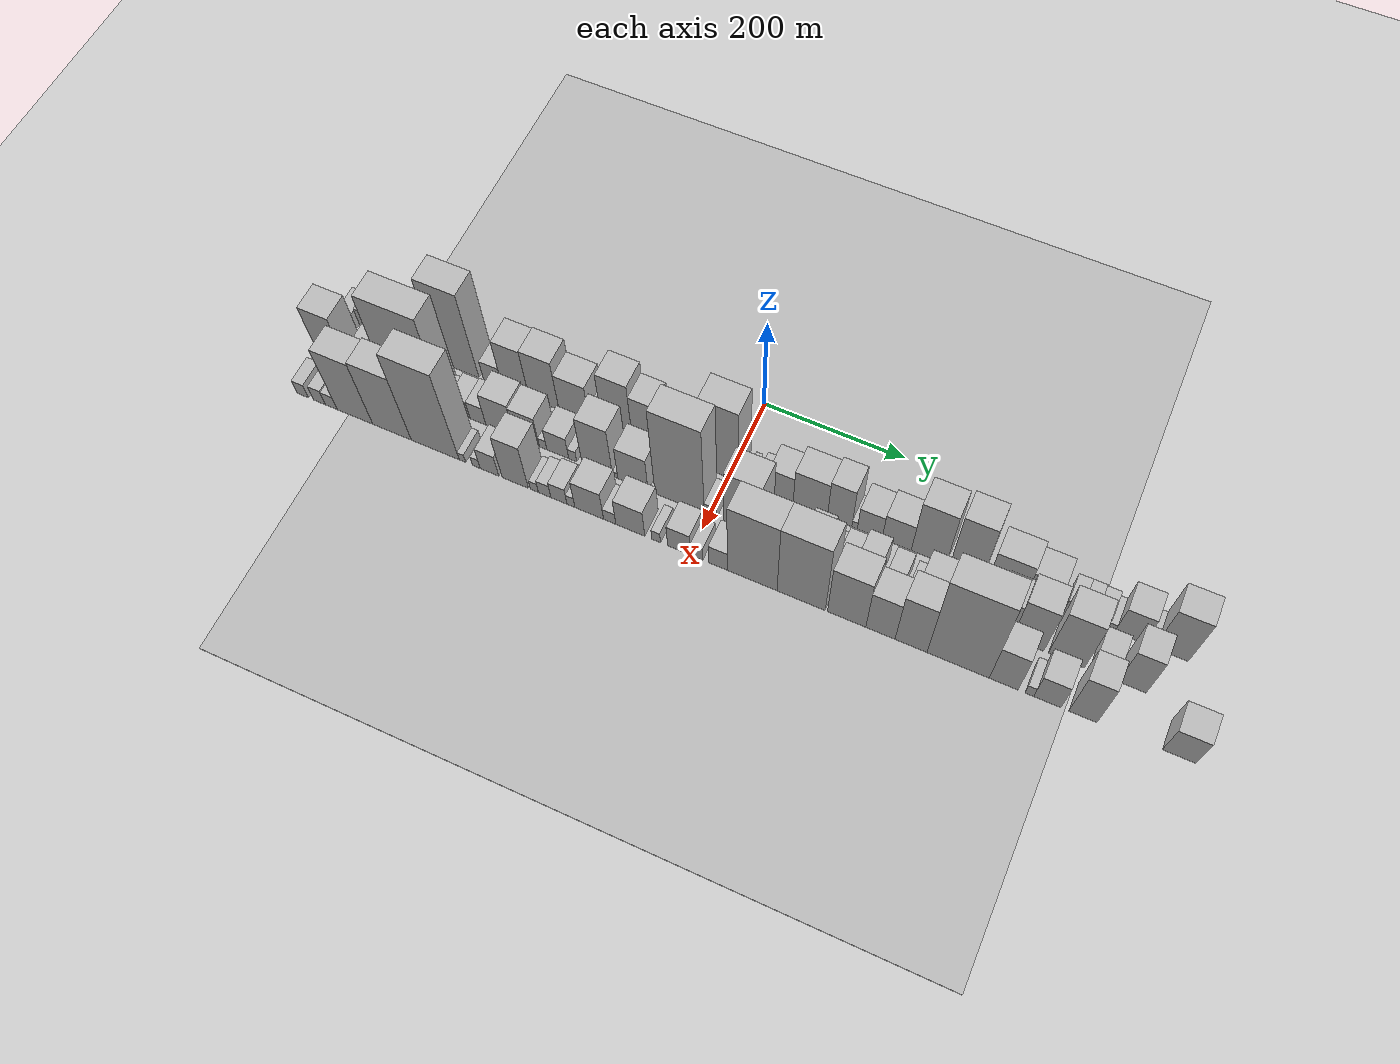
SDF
<?xml version="1.0" encoding="utf-8"?>

<sdf version="1.6">

   <world name="default">

      <gui fullscreen="0">

         <camera name="user_camera">

            <pose>-15 0 4.57585 0 0 0</pose>

            <view_controller>orbit</view_controller>

         </camera>

      </gui>

      <scene>

         <sky>

           <clouds>

             <speed>12</speed>

           </clouds>

         </sky>

         <ambient>0.4 0.4 0.4 1</ambient>

         <background>0.7 0.7 0.7 1</background>

         <shadows>1</shadows>

      </scene>

      <gravity>0 0 -9.8066</gravity>

      <magnetic_field>6e-06 2.3e-05 -4.2e-05</magnetic_field>

      <physics default="0" name="default_physics" type="ode">

         <ode>

            <solver>

               <type>quick</type>

               <iters>10</iters>

               <sor>1.0</sor>

               <use_dynamic_moi_rescaling>0</use_dynamic_moi_rescaling>

            </solver>

            <constraints>

               <cfm>0</cfm>

               <erp>0.2</erp>

               <contact_max_correcting_vel>100</contact_max_correcting_vel>

               <contact_surface_layer>0.001</contact_surface_layer>

            </constraints>

         </ode>

         <max_step_size>0.004</max_step_size>

         <real_time_factor>1</real_time_factor>

         <real_time_update_rate>250</real_time_update_rate>

      </physics>

      <light name="sun" type="directional">

         <cast_shadows>1</cast_shadows>

         <pose>0 0 10 0 0 0</pose>

         <diffuse>0.8 0.8 0.8 1</diffuse>

         <specular>0.2 0.2 0.2 1</specular>

         <attenuation>

            <range>1000</range>

            <constant>0.9</constant>

            <linear>0.01</linear>

            <quadratic>0.001</quadratic>

         </attenuation>

         <direction>-0.5 0.1 -0.9</direction>

      </light>

      <include>

         <name>ground_plane_1</name>

         <uri>model://HANNAS_ground_plane</uri>

         <pose>0 0 0  0 0 0</pose>

      </include>

      <include>

         <name>ground_plane_2</name>

         <uri>model://HANNAS_ground_plane</uri>

         <pose>100 0 0  0 0 0</pose>

      </include>

      <model name="building_1">

         <static>1</static>

         <pose frame="">100.0000 -569.5218 0 0.000000 0.000000 0.000000</pose>

         <link name="link">

            <pose frame="">0 0 18.00 0 0 0</pose>

            <collision name="collision">

               <geometry>

                  <box>

                     <size>40.0000 20.9565 36.0000</size>

                  </box>

               </geometry>

               <max_contacts>10</max_contacts>

               <surface>

                  <contact>

                     <ode/>

                  </contact>

                  <bounce/>

                  <friction>

                     <torsional>

                        <ode/>

                     </torsional>

                     <ode/>

                  </friction>

               </surface>

            </collision>

            <visual name="visual">

               <cast_shadows>0</cast_shadows>

               <geometry>

                  <box>

                     <size>40.0000 20.9565 36.0000</size>

                  </box>

               </geometry>

               <material>

                  <script>

                     <uri>model://HANNAS_wall/materials/scripts</uri>

                     <uri>model://HANNAS_wall/materials/textures</uri>

                     <name>vrc/HANNAS_wall</name>

                  </script>

               </material>

            </visual>

            <self_collide>0</self_collide>

            <enable_wind>0</enable_wind>

            <kinematic>0</kinematic>

         </link>

      </model>

      <model name="building_2">

         <static>1</static>

         <pose frame="">100.0000 -535.7136 0 0.000000 0.000000 0.000000</pose>

         <link name="link">

            <pose frame="">0 0 28.50 0 0 0</pose>

            <collision name="collision">

               <geometry>

                  <box>

                     <size>40.0000 28.6598 57.0000</size>

                  </box>

               </geometry>

               <max_contacts>10</max_contacts>

               <surface>

                  <contact>

                     <ode/>

                  </contact>

                  <bounce/>

                  <friction>

                     <torsional>

                        <ode/>

                     </torsional>

                     <ode/>

                  </friction>

               </surface>

            </collision>

            <visual name="visual">

               <cast_shadows>0</cast_shadows>

               <geometry>

                  <box>

                     <size>40.0000 28.6598 57.0000</size>

                  </box>

               </geometry>

               <material>

                  <script>

                     <uri>model://HANNAS_wall/materials/scripts</uri>

                     <uri>model://HANNAS_wall/materials/textures</uri>

                     <name>vrc/HANNAS_wall</name>

                  </script>

               </material>

            </visual>

            <self_collide>0</self_collide>

            <enable_wind>0</enable_wind>

            <kinematic>0</kinematic>

         </link>

      </model>

      <model name="building_3">

         <static>1</static>

         <pose frame="">100.0000 -504.2329 0 0.000000 0.000000 0.000000</pose>

         <link name="link">

            <pose frame="">0 0 33.00 0 0 0</pose>

            <collision name="collision">

               <geometry>

                  <box>

                     <size>40.0000 34.3018 66.0000</size>

                  </box>

               </geometry>

               <max_contacts>10</max_contacts>

               <surface>

                  <contact>

                     <ode/>

                  </contact>

                  <bounce/>

                  <friction>

                     <torsional>

                        <ode/>

                     </torsional>

                     <ode/>

                  </friction>

               </surface>

            </collision>

            <visual name="visual">

               <cast_shadows>0</cast_shadows>

               <geometry>

                  <box>

                     <size>40.0000 34.3018 66.0000</size>

                  </box>

               </geometry>

               <material>

                  <script>

                     <uri>model://HANNAS_wall/materials/scripts</uri>

                     <uri>model://HANNAS_wall/materials/textures</uri>

                     <name>vrc/HANNAS_wall</name>

                  </script>

               </material>

            </visual>

            <self_collide>0</self_collide>

            <enable_wind>0</enable_wind>

            <kinematic>0</kinematic>

         </link>

      </model>

      <model name="building_4">

         <static>1</static>

         <pose frame="">100.0000 -477.5409 0 0.000000 0.000000 0.000000</pose>

         <link name="link">

            <pose frame="">0 0 16.50 0 0 0</pose>

            <collision name="collision">

               <geometry>

                  <box>

                     <size>40.0000 19.0821 33.0000</size>

                  </box>

               </geometry>

               <max_contacts>10</max_contacts>

               <surface>

                  <contact>

                     <ode/>

                  </contact>

                  <bounce/>

                  <friction>

                     <torsional>

                        <ode/>

                     </torsional>

                     <ode/>

                  </friction>

               </surface>

            </collision>

            <visual name="visual">

               <cast_shadows>0</cast_shadows>

               <geometry>

                  <box>

                     <size>40.0000 19.0821 33.0000</size>

                  </box>

               </geometry>

               <material>

                  <script>

                     <uri>model://HANNAS_wall/materials/scripts</uri>

                     <uri>model://HANNAS_wall/materials/textures</uri>

                     <name>vrc/HANNAS_wall</name>

                  </script>

               </material>

            </visual>

            <self_collide>0</self_collide>

            <enable_wind>0</enable_wind>

            <kinematic>0</kinematic>

         </link>

      </model>

      <model name="building_5">

         <static>1</static>

         <pose frame="">100.0000 -448.7226 0 0.000000 0.000000 0.000000</pose>

         <link name="link">

            <pose frame="">0 0 34.50 0 0 0</pose>

            <collision name="collision">

               <geometry>

                  <box>

                     <size>40.0000 38.5546 69.0000</size>

                  </box>

               </geometry>

               <max_contacts>10</max_contacts>

               <surface>

                  <contact>

                     <ode/>

                  </contact>

                  <bounce/>

                  <friction>

                     <torsional>

                        <ode/>

                     </torsional>

                     <ode/>

                  </friction>

               </surface>

            </collision>

            <visual name="visual">

               <cast_shadows>0</cast_shadows>

               <geometry>

                  <box>

                     <size>40.0000 38.5546 69.0000</size>

                  </box>

               </geometry>

               <material>

                  <script>

                     <uri>model://HANNAS_wall/materials/scripts</uri>

                     <uri>model://HANNAS_wall/materials/textures</uri>

                     <name>vrc/HANNAS_wall</name>

                  </script>

               </material>

            </visual>

            <self_collide>0</self_collide>

            <enable_wind>0</enable_wind>

            <kinematic>0</kinematic>

         </link>

      </model>

      <model name="building_6">

         <static>1</static>

         <pose frame="">100.0000 -398.8562 0 0.000000 0.000000 0.000000</pose>

         <link name="link">

            <pose frame="">0 0 100.50 0 0 0</pose>

            <collision name="collision">

               <geometry>

                  <box>

                     <size>40.0000 61.1781 201.0000</size>

                  </box>

               </geometry>

               <max_contacts>10</max_contacts>

               <surface>

                  <contact>

                     <ode/>

                  </contact>

                  <bounce/>

                  <friction>

                     <torsional>

                        <ode/>

                     </torsional>

                     <ode/>

                  </friction>

               </surface>

            </collision>

            <visual name="visual">

               <cast_shadows>0</cast_shadows>

               <geometry>

                  <box>

                     <size>40.0000 61.1781 201.0000</size>

                  </box>

               </geometry>

               <material>

                  <script>

                     <uri>model://HANNAS_wall/materials/scripts</uri>

                     <uri>model://HANNAS_wall/materials/textures</uri>

                     <name>vrc/HANNAS_wall</name>

                  </script>

               </material>

            </visual>

            <self_collide>0</self_collide>

            <enable_wind>0</enable_wind>

            <kinematic>0</kinematic>

         </link>

      </model>

      <model name="building_7">

         <static>1</static>

         <pose frame="">100.0000 -346.9772 0 0.000000 0.000000 0.000000</pose>

         <link name="link">

            <pose frame="">0 0 24.00 0 0 0</pose>

            <collision name="collision">

               <geometry>

                  <box>

                     <size>40.0000 28.5800 48.0000</size>

                  </box>

               </geometry>

               <max_contacts>10</max_contacts>

               <surface>

                  <contact>

                     <ode/>

                  </contact>

                  <bounce/>

                  <friction>

                     <torsional>

                        <ode/>

                     </torsional>

                     <ode/>

                  </friction>

               </surface>

            </collision>

            <visual name="visual">

               <cast_shadows>0</cast_shadows>

               <geometry>

                  <box>

                     <size>40.0000 28.5800 48.0000</size>

                  </box>

               </geometry>

               <material>

                  <script>

                     <uri>model://HANNAS_wall/materials/scripts</uri>

                     <uri>model://HANNAS_wall/materials/textures</uri>

                     <name>vrc/HANNAS_wall</name>

                  </script>

               </material>

            </visual>

            <self_collide>0</self_collide>

            <enable_wind>0</enable_wind>

            <kinematic>0</kinematic>

         </link>

      </model>

      <model name="building_8">

         <static>1</static>

         <pose frame="">100.0000 -312.4542 0 0.000000 0.000000 0.000000</pose>

         <link name="link">

            <pose frame="">0 0 58.50 0 0 0</pose>

            <collision name="collision">

               <geometry>

                  <box>

                     <size>40.0000 40.4660 117.0000</size>

                  </box>

               </geometry>

               <max_contacts>10</max_contacts>

               <surface>

                  <contact>

                     <ode/>

                  </contact>

                  <bounce/>

                  <friction>

                     <torsional>

                        <ode/>

                     </torsional>

                     <ode/>

                  </friction>

               </surface>

            </collision>

            <visual name="visual">

               <cast_shadows>0</cast_shadows>

               <geometry>

                  <box>

                     <size>40.0000 40.4660 117.0000</size>

                  </box>

               </geometry>

               <material>

                  <script>

                     <uri>model://HANNAS_wall/materials/scripts</uri>

                     <uri>model://HANNAS_wall/materials/textures</uri>

                     <name>vrc/HANNAS_wall</name>

                  </script>

               </material>

            </visual>

            <self_collide>0</self_collide>

            <enable_wind>0</enable_wind>

            <kinematic>0</kinematic>

         </link>

      </model>

      <model name="building_9">

         <static>1</static>

         <pose frame="">100.0000 -269.7427 0 0.000000 0.000000 0.000000</pose>

         <link name="link">

            <pose frame="">0 0 60.00 0 0 0</pose>

            <collision name="collision">

               <geometry>

                  <box>

                     <size>40.0000 44.9570 120.0000</size>

                  </box>

               </geometry>

               <max_contacts>10</max_contacts>

               <surface>

                  <contact>

                     <ode/>

                  </contact>

                  <bounce/>

                  <friction>

                     <torsional>

                        <ode/>

                     </torsional>

                     <ode/>

                  </friction>

               </surface>

            </collision>

            <visual name="visual">

               <cast_shadows>0</cast_shadows>

               <geometry>

                  <box>

                     <size>40.0000 44.9570 120.0000</size>

                  </box>

               </geometry>

               <material>

                  <script>

                     <uri>model://HANNAS_wall/materials/scripts</uri>

                     <uri>model://HANNAS_wall/materials/textures</uri>

                     <name>vrc/HANNAS_wall</name>

                  </script>

               </material>

            </visual>

            <self_collide>0</self_collide>

            <enable_wind>0</enable_wind>

            <kinematic>0</kinematic>

         </link>

      </model>

      <model name="building_10">

         <static>1</static>

         <pose frame="">100.0000 -224.6503 0 0.000000 0.000000 0.000000</pose>

         <link name="link">

            <pose frame="">0 0 45.00 0 0 0</pose>

            <collision name="collision">

               <geometry>

                  <box>

                     <size>40.0000 45.2278 90.0000</size>

                  </box>

               </geometry>

               <max_contacts>10</max_contacts>

               <surface>

                  <contact>

                     <ode/>

                  </contact>

                  <bounce/>

                  <friction>

                     <torsional>

                        <ode/>

                     </torsional>

                     <ode/>

                  </friction>

               </surface>

            </collision>

            <visual name="visual">

               <cast_shadows>0</cast_shadows>

               <geometry>

                  <box>

                     <size>40.0000 45.2278 90.0000</size>

                  </box>

               </geometry>

               <material>

                  <script>

                     <uri>model://HANNAS_wall/materials/scripts</uri>

                     <uri>model://HANNAS_wall/materials/textures</uri>

                     <name>vrc/HANNAS_wall</name>

                  </script>

               </material>

            </visual>

            <self_collide>0</self_collide>

            <enable_wind>0</enable_wind>

            <kinematic>0</kinematic>

         </link>

      </model>

      <model name="building_11">

         <static>1</static>

         <pose frame="">100.0000 -192.2849 0 0.000000 0.000000 0.000000</pose>

         <link name="link">

            <pose frame="">0 0 18.00 0 0 0</pose>

            <collision name="collision">

               <geometry>

                  <box>

                     <size>40.0000 19.5030 36.0000</size>

                  </box>

               </geometry>

               <max_contacts>10</max_contacts>

               <surface>

                  <contact>

                     <ode/>

                  </contact>

                  <bounce/>

                  <friction>

                     <torsional>

                        <ode/>

                     </torsional>

                     <ode/>

                  </friction>

               </surface>

            </collision>

            <visual name="visual">

               <cast_shadows>0</cast_shadows>

               <geometry>

                  <box>

                     <size>40.0000 19.5030 36.0000</size>

                  </box>

               </geometry>

               <material>

                  <script>

                     <uri>model://HANNAS_wall/materials/scripts</uri>

                     <uri>model://HANNAS_wall/materials/textures</uri>

                     <name>vrc/HANNAS_wall</name>

                  </script>

               </material>

            </visual>

            <self_collide>0</self_collide>

            <enable_wind>0</enable_wind>

            <kinematic>0</kinematic>

         </link>

      </model>

      <model name="building_12">

         <static>1</static>

         <pose frame="">100.0000 -160.6596 0 0.000000 0.000000 0.000000</pose>

         <link name="link">

            <pose frame="">0 0 69.00 0 0 0</pose>

            <collision name="collision">

               <geometry>

                  <box>

                     <size>40.0000 43.7476 138.0000</size>

                  </box>

               </geometry>

               <max_contacts>10</max_contacts>

               <surface>

                  <contact>

                     <ode/>

                  </contact>

                  <bounce/>

                  <friction>

                     <torsional>

                        <ode/>

                     </torsional>

                     <ode/>

                  </friction>

               </surface>

            </collision>

            <visual name="visual">

               <cast_shadows>0</cast_shadows>

               <geometry>

                  <box>

                     <size>40.0000 43.7476 138.0000</size>

                  </box>

               </geometry>

               <material>

                  <script>

                     <uri>model://HANNAS_wall/materials/scripts</uri>

                     <uri>model://HANNAS_wall/materials/textures</uri>

                     <name>vrc/HANNAS_wall</name>

                  </script>

               </material>

            </visual>

            <self_collide>0</self_collide>

            <enable_wind>0</enable_wind>

            <kinematic>0</kinematic>

         </link>

      </model>

      <model name="building_13">

         <static>1</static>

         <pose frame="">100.0000 -121.3531 0 0.000000 0.000000 0.000000</pose>

         <link name="link">

            <pose frame="">0 0 55.50 0 0 0</pose>

            <collision name="collision">

               <geometry>

                  <box>

                     <size>40.0000 34.8656 111.0000</size>

                  </box>

               </geometry>

               <max_contacts>10</max_contacts>

               <surface>

                  <contact>

                     <ode/>

                  </contact>

                  <bounce/>

                  <friction>

                     <torsional>

                        <ode/>

                     </torsional>

                     <ode/>

                  </friction>

               </surface>

            </collision>

            <visual name="visual">

               <cast_shadows>0</cast_shadows>

               <geometry>

                  <box>

                     <size>40.0000 34.8656 111.0000</size>

                  </box>

               </geometry>

               <material>

                  <script>

                     <uri>model://HANNAS_wall/materials/scripts</uri>

                     <uri>model://HANNAS_wall/materials/textures</uri>

                     <name>vrc/HANNAS_wall</name>

                  </script>

               </material>

            </visual>

            <self_collide>0</self_collide>

            <enable_wind>0</enable_wind>

            <kinematic>0</kinematic>

         </link>

      </model>

      <model name="building_14">

         <static>1</static>

         <pose frame="">100.0000 -86.2994 0 0.000000 0.000000 0.000000</pose>

         <link name="link">

            <pose frame="">0 0 24.00 0 0 0</pose>

            <collision name="collision">

               <geometry>

                  <box>

                     <size>40.0000 25.2418 48.0000</size>

                  </box>

               </geometry>

               <max_contacts>10</max_contacts>

               <surface>

                  <contact>

                     <ode/>

                  </contact>

                  <bounce/>

                  <friction>

                     <torsional>

                        <ode/>

                     </torsional>

                     <ode/>

                  </friction>

               </surface>

            </collision>

            <visual name="visual">

               <cast_shadows>0</cast_shadows>

               <geometry>

                  <box>

                     <size>40.0000 25.2418 48.0000</size>

                  </box>

               </geometry>

               <material>

                  <script>

                     <uri>model://HANNAS_wall/materials/scripts</uri>

                     <uri>model://HANNAS_wall/materials/textures</uri>

                     <name>vrc/HANNAS_wall</name>

                  </script>

               </material>

            </visual>

            <self_collide>0</self_collide>

            <enable_wind>0</enable_wind>

            <kinematic>0</kinematic>

         </link>

      </model>

      <model name="building_15">

         <static>1</static>

         <pose frame="">100.0000 -57.0559 0 0.000000 0.000000 0.000000</pose>

         <link name="link">

            <pose frame="">0 0 30.00 0 0 0</pose>

            <collision name="collision">

               <geometry>

                  <box>

                     <size>40.0000 33.2452 60.0000</size>

                  </box>

               </geometry>

               <max_contacts>10</max_contacts>

               <surface>

                  <contact>

                     <ode/>

                  </contact>

                  <bounce/>

                  <friction>

                     <torsional>

                        <ode/>

                     </torsional>

                     <ode/>

                  </friction>

               </surface>

            </collision>

            <visual name="visual">

               <cast_shadows>0</cast_shadows>

               <geometry>

                  <box>

                     <size>40.0000 33.2452 60.0000</size>

                  </box>

               </geometry>

               <material>

                  <script>

                     <uri>model://HANNAS_wall/materials/scripts</uri>

                     <uri>model://HANNAS_wall/materials/textures</uri>

                     <name>vrc/HANNAS_wall</name>

                  </script>

               </material>

            </visual>

            <self_collide>0</self_collide>

            <enable_wind>0</enable_wind>

            <kinematic>0</kinematic>

         </link>

      </model>

      <model name="building_16">

         <static>1</static>

         <pose frame="">100.0000 -13.0072 0 0.000000 0.000000 0.000000</pose>

         <link name="link">

            <pose frame="">0 0 90.00 0 0 0</pose>

            <collision name="collision">

               <geometry>

                  <box>

                     <size>40.0000 54.8522 180.0000</size>

                  </box>

               </geometry>

               <max_contacts>10</max_contacts>

               <surface>

                  <contact>

                     <ode/>

                  </contact>

                  <bounce/>

                  <friction>

                     <torsional>

                        <ode/>

                     </torsional>

                     <ode/>

                  </friction>

               </surface>

            </collision>

            <visual name="visual">

               <cast_shadows>0</cast_shadows>

               <geometry>

                  <box>

                     <size>40.0000 54.8522 180.0000</size>

                  </box>

               </geometry>

               <material>

                  <script>

                     <uri>model://HANNAS_wall/materials/scripts</uri>

                     <uri>model://HANNAS_wall/materials/textures</uri>

                     <name>vrc/HANNAS_wall</name>

                  </script>

               </material>

            </visual>

            <self_collide>0</self_collide>

            <enable_wind>0</enable_wind>

            <kinematic>0</kinematic>

         </link>

      </model>

      <model name="building_17">

         <static>1</static>

         <pose frame="">100.0000 26.8543 0 0.000000 0.000000 0.000000</pose>

         <link name="link">

            <pose frame="">0 0 10.50 0 0 0</pose>

            <collision name="collision">

               <geometry>

                  <box>

                     <size>40.0000 8.8710 21.0000</size>

                  </box>

               </geometry>

               <max_contacts>10</max_contacts>

               <surface>

                  <contact>

                     <ode/>

                  </contact>

                  <bounce/>

                  <friction>

                     <torsional>

                        <ode/>

                     </torsional>

                     <ode/>

                  </friction>

               </surface>

            </collision>

            <visual name="visual">

               <cast_shadows>0</cast_shadows>

               <geometry>

                  <box>

                     <size>40.0000 8.8710 21.0000</size>

                  </box>

               </geometry>

               <material>

                  <script>

                     <uri>model://HANNAS_wall/materials/scripts</uri>

                     <uri>model://HANNAS_wall/materials/textures</uri>

                     <name>vrc/HANNAS_wall</name>

                  </script>

               </material>

            </visual>

            <self_collide>0</self_collide>

            <enable_wind>0</enable_wind>

            <kinematic>0</kinematic>

         </link>

      </model>

      <model name="building_18">

         <static>1</static>

         <pose frame="">100.0000 47.9079 0 0.000000 0.000000 0.000000</pose>

         <link name="link">

            <pose frame="">0 0 16.50 0 0 0</pose>

            <collision name="collision">

               <geometry>

                  <box>

                     <size>40.0000 17.2362 33.0000</size>

                  </box>

               </geometry>

               <max_contacts>10</max_contacts>

               <surface>

                  <contact>

                     <ode/>

                  </contact>

                  <bounce/>

                  <friction>

                     <torsional>

                        <ode/>

                     </torsional>

                     <ode/>

                  </friction>

               </surface>

            </collision>

            <visual name="visual">

               <cast_shadows>0</cast_shadows>

               <geometry>

                  <box>

                     <size>40.0000 17.2362 33.0000</size>

                  </box>

               </geometry>

               <material>

                  <script>

                     <uri>model://HANNAS_wall/materials/scripts</uri>

                     <uri>model://HANNAS_wall/materials/textures</uri>

                     <name>vrc/HANNAS_wall</name>

                  </script>

               </material>

            </visual>

            <self_collide>0</self_collide>

            <enable_wind>0</enable_wind>

            <kinematic>0</kinematic>

         </link>

      </model>

      <model name="building_19">

         <static>1</static>

         <pose frame="">100.0000 74.0982 0 0.000000 0.000000 0.000000</pose>

         <link name="link">

            <pose frame="">0 0 34.50 0 0 0</pose>

            <collision name="collision">

               <geometry>

                  <box>

                     <size>40.0000 35.1444 69.0000</size>

                  </box>

               </geometry>

               <max_contacts>10</max_contacts>

               <surface>

                  <contact>

                     <ode/>

                  </contact>

                  <bounce/>

                  <friction>

                     <torsional>

                        <ode/>

                     </torsional>

                     <ode/>

                  </friction>

               </surface>

            </collision>

            <visual name="visual">

               <cast_shadows>0</cast_shadows>

               <geometry>

                  <box>

                     <size>40.0000 35.1444 69.0000</size>

                  </box>

               </geometry>

               <material>

                  <script>

                     <uri>model://HANNAS_wall/materials/scripts</uri>

                     <uri>model://HANNAS_wall/materials/textures</uri>

                     <name>vrc/HANNAS_wall</name>

                  </script>

               </material>

            </visual>

            <self_collide>0</self_collide>

            <enable_wind>0</enable_wind>

            <kinematic>0</kinematic>

         </link>

      </model>

      <model name="building_20">

         <static>1</static>

         <pose frame="">100.0000 115.5759 0 0.000000 0.000000 0.000000</pose>

         <link name="link">

            <pose frame="">0 0 45.00 0 0 0</pose>

            <collision name="collision">

               <geometry>

                  <box>

                     <size>40.0000 47.8111 90.0000</size>

                  </box>

               </geometry>

               <max_contacts>10</max_contacts>

               <surface>

                  <contact>

                     <ode/>

                  </contact>

                  <bounce/>

                  <friction>

                     <torsional>

                        <ode/>

                     </torsional>

                     <ode/>

                  </friction>

               </surface>

            </collision>

            <visual name="visual">

               <cast_shadows>0</cast_shadows>

               <geometry>

                  <box>

                     <size>40.0000 47.8111 90.0000</size>

                  </box>

               </geometry>

               <material>

                  <script>

                     <uri>model://HANNAS_wall/materials/scripts</uri>

                     <uri>model://HANNAS_wall/materials/textures</uri>

                     <name>vrc/HANNAS_wall</name>

                  </script>

               </material>

            </visual>

            <self_collide>0</self_collide>

            <enable_wind>0</enable_wind>

            <kinematic>0</kinematic>

         </link>

      </model>

      <model name="building_21">

         <static>1</static>

         <pose frame="">100.0000 156.3765 0 0.000000 0.000000 0.000000</pose>

         <link name="link">

            <pose frame="">0 0 49.50 0 0 0</pose>

            <collision name="collision">

               <geometry>

                  <box>

                     <size>40.0000 33.7900 99.0000</size>

                  </box>

               </geometry>

               <max_contacts>10</max_contacts>

               <surface>

                  <contact>

                     <ode/>

                  </contact>

                  <bounce/>

                  <friction>

                     <torsional>

                        <ode/>

                     </torsional>

                     <ode/>

                  </friction>

               </surface>

            </collision>

            <visual name="visual">

               <cast_shadows>0</cast_shadows>

               <geometry>

                  <box>

                     <size>40.0000 33.7900 99.0000</size>

                  </box>

               </geometry>

               <material>

                  <script>

                     <uri>model://HANNAS_wall/materials/scripts</uri>

                     <uri>model://HANNAS_wall/materials/textures</uri>

                     <name>vrc/HANNAS_wall</name>

                  </script>

               </material>

            </visual>

            <self_collide>0</self_collide>

            <enable_wind>0</enable_wind>

            <kinematic>0</kinematic>

         </link>

      </model>

      <model name="building_22">

         <static>1</static>

         <pose frame="">100.0000 177.1312 0 0.000000 0.000000 0.000000</pose>

         <link name="link">

            <pose frame="">0 0 9.00 0 0 0</pose>

            <collision name="collision">

               <geometry>

                  <box>

                     <size>40.0000 7.7195 18.0000</size>

                  </box>

               </geometry>

               <max_contacts>10</max_contacts>

               <surface>

                  <contact>

                     <ode/>

                  </contact>

                  <bounce/>

                  <friction>

                     <torsional>

                        <ode/>

                     </torsional>

                     <ode/>

                  </friction>

               </surface>

            </collision>

            <visual name="visual">

               <cast_shadows>0</cast_shadows>

               <geometry>

                  <box>

                     <size>40.0000 7.7195 18.0000</size>

                  </box>

               </geometry>

               <material>

                  <script>

                     <uri>model://HANNAS_wall/materials/scripts</uri>

                     <uri>model://HANNAS_wall/materials/textures</uri>

                     <name>vrc/HANNAS_wall</name>

                  </script>

               </material>

            </visual>

            <self_collide>0</self_collide>

            <enable_wind>0</enable_wind>

            <kinematic>0</kinematic>

         </link>

      </model>

      <model name="building_23">

         <static>1</static>

         <pose frame="">100.0000 198.0240 0 0.000000 0.000000 0.000000</pose>

         <link name="link">

            <pose frame="">0 0 30.00 0 0 0</pose>

            <collision name="collision">

               <geometry>

                  <box>

                     <size>40.0000 34.0659 60.0000</size>

                  </box>

               </geometry>

               <max_contacts>10</max_contacts>

               <surface>

                  <contact>

                     <ode/>

                  </contact>

                  <bounce/>

                  <friction>

                     <torsional>

                        <ode/>

                     </torsional>

                     <ode/>

                  </friction>

               </surface>

            </collision>

            <visual name="visual">

               <cast_shadows>0</cast_shadows>

               <geometry>

                  <box>

                     <size>40.0000 34.0659 60.0000</size>

                  </box>

               </geometry>

               <material>

                  <script>

                     <uri>model://HANNAS_wall/materials/scripts</uri>

                     <uri>model://HANNAS_wall/materials/textures</uri>

                     <name>vrc/HANNAS_wall</name>

                  </script>

               </material>

            </visual>

            <self_collide>0</self_collide>

            <enable_wind>0</enable_wind>

            <kinematic>0</kinematic>

         </link>

      </model>

      <model name="building_24">

         <static>1</static>

         <pose frame="">100.0000 234.9716 0 0.000000 0.000000 0.000000</pose>

         <link name="link">

            <pose frame="">0 0 34.50 0 0 0</pose>

            <collision name="collision">

               <geometry>

                  <box>

                     <size>40.0000 39.8295 69.0000</size>

                  </box>

               </geometry>

               <max_contacts>10</max_contacts>

               <surface>

                  <contact>

                     <ode/>

                  </contact>

                  <bounce/>

                  <friction>

                     <torsional>

                        <ode/>

                     </torsional>

                     <ode/>

                  </friction>

               </surface>

            </collision>

            <visual name="visual">

               <cast_shadows>0</cast_shadows>

               <geometry>

                  <box>

                     <size>40.0000 39.8295 69.0000</size>

                  </box>

               </geometry>

               <material>

                  <script>

                     <uri>model://HANNAS_wall/materials/scripts</uri>

                     <uri>model://HANNAS_wall/materials/textures</uri>

                     <name>vrc/HANNAS_wall</name>

                  </script>

               </material>

            </visual>

            <self_collide>0</self_collide>

            <enable_wind>0</enable_wind>

            <kinematic>0</kinematic>

         </link>

      </model>

      <model name="building_25">

         <static>1</static>

         <pose frame="">100.0000 278.4877 0 0.000000 0.000000 0.000000</pose>

         <link name="link">

            <pose frame="">0 0 69.00 0 0 0</pose>

            <collision name="collision">

               <geometry>

                  <box>

                     <size>40.0000 47.2026 138.0000</size>

                  </box>

               </geometry>

               <max_contacts>10</max_contacts>

               <surface>

                  <contact>

                     <ode/>

                  </contact>

                  <bounce/>

                  <friction>

                     <torsional>

                        <ode/>

                     </torsional>

                     <ode/>

                  </friction>

               </surface>

            </collision>

            <visual name="visual">

               <cast_shadows>0</cast_shadows>

               <geometry>

                  <box>

                     <size>40.0000 47.2026 138.0000</size>

                  </box>

               </geometry>

               <material>

                  <script>

                     <uri>model://HANNAS_wall/materials/scripts</uri>

                     <uri>model://HANNAS_wall/materials/textures</uri>

                     <name>vrc/HANNAS_wall</name>

                  </script>

               </material>

            </visual>

            <self_collide>0</self_collide>

            <enable_wind>0</enable_wind>

            <kinematic>0</kinematic>

         </link>

      </model>

      <model name="building_26">

         <static>1</static>

         <pose frame="">100.0000 329.0434 0 0.000000 0.000000 0.000000</pose>

         <link name="link">

            <pose frame="">0 0 72.00 0 0 0</pose>

            <collision name="collision">

               <geometry>

                  <box>

                     <size>40.0000 43.9088 144.0000</size>

                  </box>

               </geometry>

               <max_contacts>10</max_contacts>

               <surface>

                  <contact>

                     <ode/>

                  </contact>

                  <bounce/>

                  <friction>

                     <torsional>

                        <ode/>

                     </torsional>

                     <ode/>

                  </friction>

               </surface>

            </collision>

            <visual name="visual">

               <cast_shadows>0</cast_shadows>

               <geometry>

                  <box>

                     <size>40.0000 43.9088 144.0000</size>

                  </box>

               </geometry>

               <material>

                  <script>

                     <uri>model://HANNAS_wall/materials/scripts</uri>

                     <uri>model://HANNAS_wall/materials/textures</uri>

                     <name>vrc/HANNAS_wall</name>

                  </script>

               </material>

            </visual>

            <self_collide>0</self_collide>

            <enable_wind>0</enable_wind>

            <kinematic>0</kinematic>

         </link>

      </model>

      <model name="building_27">

         <static>1</static>

         <pose frame="">100.0000 383.1958 0 0.000000 0.000000 0.000000</pose>

         <link name="link">

            <pose frame="">0 0 43.50 0 0 0</pose>

            <collision name="collision">

               <geometry>

                  <box>

                     <size>40.0000 50.3961 87.0000</size>

                  </box>

               </geometry>

               <max_contacts>10</max_contacts>

               <surface>

                  <contact>

                     <ode/>

                  </contact>

                  <bounce/>

                  <friction>

                     <torsional>

                        <ode/>

                     </torsional>

                     <ode/>

                  </friction>

               </surface>

            </collision>

            <visual name="visual">

               <cast_shadows>0</cast_shadows>

               <geometry>

                  <box>

                     <size>40.0000 50.3961 87.0000</size>

                  </box>

               </geometry>

               <material>

                  <script>

                     <uri>model://HANNAS_wall/materials/scripts</uri>

                     <uri>model://HANNAS_wall/materials/textures</uri>

                     <name>vrc/HANNAS_wall</name>

                  </script>

               </material>

            </visual>

            <self_collide>0</self_collide>

            <enable_wind>0</enable_wind>

            <kinematic>0</kinematic>

         </link>

      </model>

      <model name="building_28">

         <static>1</static>

         <pose frame="">100.0000 428.4094 0 0.000000 0.000000 0.000000</pose>

         <link name="link">

            <pose frame="">0 0 36.00 0 0 0</pose>

            <collision name="collision">

               <geometry>

                  <box>

                     <size>40.0000 40.0310 72.0000</size>

                  </box>

               </geometry>

               <max_contacts>10</max_contacts>

               <surface>

                  <contact>

                     <ode/>

                  </contact>

                  <bounce/>

                  <friction>

                     <torsional>

                        <ode/>

                     </torsional>

                     <ode/>

                  </friction>

               </surface>

            </collision>

            <visual name="visual">

               <cast_shadows>0</cast_shadows>

               <geometry>

                  <box>

                     <size>40.0000 40.0310 72.0000</size>

                  </box>

               </geometry>

               <material>

                  <script>

                     <uri>model://HANNAS_wall/materials/scripts</uri>

                     <uri>model://HANNAS_wall/materials/textures</uri>

                     <name>vrc/HANNAS_wall</name>

                  </script>

               </material>

            </visual>

            <self_collide>0</self_collide>

            <enable_wind>0</enable_wind>

            <kinematic>0</kinematic>

         </link>

      </model>

      <model name="building_29">

         <static>1</static>

         <pose frame="">100.0000 467.8048 0 0.000000 0.000000 0.000000</pose>

         <link name="link">

            <pose frame="">0 0 18.00 0 0 0</pose>

            <collision name="collision">

               <geometry>

                  <box>

                     <size>40.0000 18.7598 36.0000</size>

                  </box>

               </geometry>

               <max_contacts>10</max_contacts>

               <surface>

                  <contact>

                     <ode/>

                  </contact>

                  <bounce/>

                  <friction>

                     <torsional>

                        <ode/>

                     </torsional>

                     <ode/>

                  </friction>

               </surface>

            </collision>

            <visual name="visual">

               <cast_shadows>0</cast_shadows>

               <geometry>

                  <box>

                     <size>40.0000 18.7598 36.0000</size>

                  </box>

               </geometry>

               <material>

                  <script>

                     <uri>model://HANNAS_wall/materials/scripts</uri>

                     <uri>model://HANNAS_wall/materials/textures</uri>

                     <name>vrc/HANNAS_wall</name>

                  </script>

               </material>

            </visual>

            <self_collide>0</self_collide>

            <enable_wind>0</enable_wind>

            <kinematic>0</kinematic>

         </link>

      </model>

      <model name="building_30">

         <static>1</static>

         <pose frame="">100.0000 486.4014 0 0.000000 0.000000 0.000000</pose>

         <link name="link">

            <pose frame="">0 0 18.00 0 0 0</pose>

            <collision name="collision">

               <geometry>

                  <box>

                     <size>40.0000 18.4333 36.0000</size>

                  </box>

               </geometry>

               <max_contacts>10</max_contacts>

               <surface>

                  <contact>

                     <ode/>

                  </contact>

                  <bounce/>

                  <friction>

                     <torsional>

                        <ode/>

                     </torsional>

                     <ode/>

                  </friction>

               </surface>

            </collision>

            <visual name="visual">

               <cast_shadows>0</cast_shadows>

               <geometry>

                  <box>

                     <size>40.0000 18.4333 36.0000</size>

                  </box>

               </geometry>

               <material>

                  <script>

                     <uri>model://HANNAS_wall/materials/scripts</uri>

                     <uri>model://HANNAS_wall/materials/textures</uri>

                     <name>vrc/HANNAS_wall</name>

                  </script>

               </material>

            </visual>

            <self_collide>0</self_collide>

            <enable_wind>0</enable_wind>

            <kinematic>0</kinematic>

         </link>

      </model>

      <model name="building_31">

         <static>1</static>

         <pose frame="">100.0000 505.3228 0 0.000000 0.000000 0.000000</pose>

         <link name="link">

            <pose frame="">0 0 16.50 0 0 0</pose>

            <collision name="collision">

               <geometry>

                  <box>

                     <size>40.0000 19.4096 33.0000</size>

                  </box>

               </geometry>

               <max_contacts>10</max_contacts>

               <surface>

                  <contact>

                     <ode/>

                  </contact>

                  <bounce/>

                  <friction>

                     <torsional>

                        <ode/>

                     </torsional>

                     <ode/>

                  </friction>

               </surface>

            </collision>

            <visual name="visual">

               <cast_shadows>0</cast_shadows>

               <geometry>

                  <box>

                     <size>40.0000 19.4096 33.0000</size>

                  </box>

               </geometry>

               <material>

                  <script>

                     <uri>model://HANNAS_wall/materials/scripts</uri>

                     <uri>model://HANNAS_wall/materials/textures</uri>

                     <name>vrc/HANNAS_wall</name>

                  </script>

               </material>

            </visual>

            <self_collide>0</self_collide>

            <enable_wind>0</enable_wind>

            <kinematic>0</kinematic>

         </link>

      </model>

      <model name="building_32">

         <static>1</static>

         <pose frame="">100.0000 519.8692 0 0.000000 0.000000 0.000000</pose>

         <link name="link">

            <pose frame="">0 0 10.50 0 0 0</pose>

            <collision name="collision">

               <geometry>

                  <box>

                     <size>40.0000 9.6833 21.0000</size>

                  </box>

               </geometry>

               <max_contacts>10</max_contacts>

               <surface>

                  <contact>

                     <ode/>

                  </contact>

                  <bounce/>

                  <friction>

                     <torsional>

                        <ode/>

                     </torsional>

                     <ode/>

                  </friction>

               </surface>

            </collision>

            <visual name="visual">

               <cast_shadows>0</cast_shadows>

               <geometry>

                  <box>

                     <size>40.0000 9.6833 21.0000</size>

                  </box>

               </geometry>

               <material>

                  <script>

                     <uri>model://HANNAS_wall/materials/scripts</uri>

                     <uri>model://HANNAS_wall/materials/textures</uri>

                     <name>vrc/HANNAS_wall</name>

                  </script>

               </material>

            </visual>

            <self_collide>0</self_collide>

            <enable_wind>0</enable_wind>

            <kinematic>0</kinematic>

         </link>

      </model>

      <model name="building_33">

         <static>1</static>

         <pose frame="">100.0000 543.5015 0 0.000000 0.000000 0.000000</pose>

         <link name="link">

            <pose frame="">0 0 37.50 0 0 0</pose>

            <collision name="collision">

               <geometry>

                  <box>

                     <size>40.0000 37.5813 75.0000</size>

                  </box>

               </geometry>

               <max_contacts>10</max_contacts>

               <surface>

                  <contact>

                     <ode/>

                  </contact>

                  <bounce/>

                  <friction>

                     <torsional>

                        <ode/>

                     </torsional>

                     <ode/>

                  </friction>

               </surface>

            </collision>

            <visual name="visual">

               <cast_shadows>0</cast_shadows>

               <geometry>

                  <box>

                     <size>40.0000 37.5813 75.0000</size>

                  </box>

               </geometry>

               <material>

                  <script>

                     <uri>model://HANNAS_wall/materials/scripts</uri>

                     <uri>model://HANNAS_wall/materials/textures</uri>

                     <name>vrc/HANNAS_wall</name>

                  </script>

               </material>

            </visual>

            <self_collide>0</self_collide>

            <enable_wind>0</enable_wind>

            <kinematic>0</kinematic>

         </link>

      </model>

      <model name="building_34">

         <static>1</static>

         <pose frame="">100.0000 568.5206 0 0.000000 0.000000 0.000000</pose>

         <link name="link">

            <pose frame="">0 0 13.50 0 0 0</pose>

            <collision name="collision">

               <geometry>

                  <box>

                     <size>40.0000 12.4568 27.0000</size>

                  </box>

               </geometry>

               <max_contacts>10</max_contacts>

               <surface>

                  <contact>

                     <ode/>

                  </contact>

                  <bounce/>

                  <friction>

                     <torsional>

                        <ode/>

                     </torsional>

                     <ode/>

                  </friction>

               </surface>

            </collision>

            <visual name="visual">

               <cast_shadows>0</cast_shadows>

               <geometry>

                  <box>

                     <size>40.0000 12.4568 27.0000</size>

                  </box>

               </geometry>

               <material>

                  <script>

                     <uri>model://HANNAS_wall/materials/scripts</uri>

                     <uri>model://HANNAS_wall/materials/textures</uri>

                     <name>vrc/HANNAS_wall</name>

                  </script>

               </material>

            </visual>

            <self_collide>0</self_collide>

            <enable_wind>0</enable_wind>

            <kinematic>0</kinematic>

         </link>

      </model>

      <model name="building_35">

         <static>1</static>

         <pose frame="">100.0000 596.9426 0 0.000000 0.000000 0.000000</pose>

         <link name="link">

            <pose frame="">0 0 60.00 0 0 0</pose>

            <collision name="collision">

               <geometry>

                  <box>

                     <size>40.0000 44.3872 120.0000</size>

                  </box>

               </geometry>

               <max_contacts>10</max_contacts>

               <surface>

                  <contact>

                     <ode/>

                  </contact>

                  <bounce/>

                  <friction>

                     <torsional>

                        <ode/>

                     </torsional>

                     <ode/>

                  </friction>

               </surface>

            </collision>

            <visual name="visual">

               <cast_shadows>0</cast_shadows>

               <geometry>

                  <box>

                     <size>40.0000 44.3872 120.0000</size>

                  </box>

               </geometry>

               <material>

                  <script>

                     <uri>model://HANNAS_wall/materials/scripts</uri>

                     <uri>model://HANNAS_wall/materials/textures</uri>

                     <name>vrc/HANNAS_wall</name>

                  </script>

               </material>

            </visual>

            <self_collide>0</self_collide>

            <enable_wind>0</enable_wind>

            <kinematic>0</kinematic>

         </link>

      </model>

      <model name="building_36">

         <static>1</static>

         <pose frame="">160.0000 -557.7278 0 0.000000 0.000000 0.000000</pose>

         <link name="link">

            <pose frame="">0 0 63.00 0 0 0</pose>

            <collision name="collision">

               <geometry>

                  <box>

                     <size>40.0000 44.5443 126.0000</size>

                  </box>

               </geometry>

               <max_contacts>10</max_contacts>

               <surface>

                  <contact>

                     <ode/>

                  </contact>

                  <bounce/>

                  <friction>

                     <torsional>

                        <ode/>

                     </torsional>

                     <ode/>

                  </friction>

               </surface>

            </collision>

            <visual name="visual">

               <cast_shadows>0</cast_shadows>

               <geometry>

                  <box>

                     <size>40.0000 44.5443 126.0000</size>

                  </box>

               </geometry>

               <material>

                  <script>

                     <uri>model://HANNAS_wall/materials/scripts</uri>

                     <uri>model://HANNAS_wall/materials/textures</uri>

                     <name>vrc/HANNAS_wall</name>

                  </script>

               </material>

            </visual>

            <self_collide>0</self_collide>

            <enable_wind>0</enable_wind>

            <kinematic>0</kinematic>

         </link>

      </model>

      <model name="building_37">

         <static>1</static>

         <pose frame="">160.0000 -522.8158 0 0.000000 0.000000 0.000000</pose>

         <link name="link">

            <pose frame="">0 0 7.50 0 0 0</pose>

            <collision name="collision">

               <geometry>

                  <box>

                     <size>40.0000 7.2797 15.0000</size>

                  </box>

               </geometry>

               <max_contacts>10</max_contacts>

               <surface>

                  <contact>

                     <ode/>

                  </contact>

                  <bounce/>

                  <friction>

                     <torsional>

                        <ode/>

                     </torsional>

                     <ode/>

                  </friction>

               </surface>

            </collision>

            <visual name="visual">

               <cast_shadows>0</cast_shadows>

               <geometry>

                  <box>

                     <size>40.0000 7.2797 15.0000</size>

                  </box>

               </geometry>

               <material>

                  <script>

                     <uri>model://HANNAS_wall/materials/scripts</uri>

                     <uri>model://HANNAS_wall/materials/textures</uri>

                     <name>vrc/HANNAS_wall</name>

                  </script>

               </material>

            </visual>

            <self_collide>0</self_collide>

            <enable_wind>0</enable_wind>

            <kinematic>0</kinematic>

         </link>

      </model>

      <model name="building_38">

         <static>1</static>

         <pose frame="">160.0000 -499.9888 0 0.000000 0.000000 0.000000</pose>

         <link name="link">

            <pose frame="">0 0 36.00 0 0 0</pose>

            <collision name="collision">

               <geometry>

                  <box>

                     <size>40.0000 38.3744 72.0000</size>

                  </box>

               </geometry>

               <max_contacts>10</max_contacts>

               <surface>

                  <contact>

                     <ode/>

                  </contact>

                  <bounce/>

                  <friction>

                     <torsional>

                        <ode/>

                     </torsional>

                     <ode/>

                  </friction>

               </surface>

            </collision>

            <visual name="visual">

               <cast_shadows>0</cast_shadows>

               <geometry>

                  <box>

                     <size>40.0000 38.3744 72.0000</size>

                  </box>

               </geometry>

               <material>

                  <script>

                     <uri>model://HANNAS_wall/materials/scripts</uri>

                     <uri>model://HANNAS_wall/materials/textures</uri>

                     <name>vrc/HANNAS_wall</name>

                  </script>

               </material>

            </visual>

            <self_collide>0</self_collide>

            <enable_wind>0</enable_wind>

            <kinematic>0</kinematic>

         </link>

      </model>

      <model name="building_39">

         <static>1</static>

         <pose frame="">160.0000 -431.4649 0 0.000000 0.000000 0.000000</pose>

         <link name="link">

            <pose frame="">0 0 109.50 0 0 0</pose>

            <collision name="collision">

               <geometry>

                  <box>

                     <size>40.0000 86.6733 219.0000</size>

                  </box>

               </geometry>

               <max_contacts>10</max_contacts>

               <surface>

                  <contact>

                     <ode/>

                  </contact>

                  <bounce/>

                  <friction>

                     <torsional>

                        <ode/>

                     </torsional>

                     <ode/>

                  </friction>

               </surface>

            </collision>

            <visual name="visual">

               <cast_shadows>0</cast_shadows>

               <geometry>

                  <box>

                     <size>40.0000 86.6733 219.0000</size>

                  </box>

               </geometry>

               <material>

                  <script>

                     <uri>model://HANNAS_wall/materials/scripts</uri>

                     <uri>model://HANNAS_wall/materials/textures</uri>

                     <name>vrc/HANNAS_wall</name>

                  </script>

               </material>

            </visual>

            <self_collide>0</self_collide>

            <enable_wind>0</enable_wind>

            <kinematic>0</kinematic>

         </link>

      </model>

      <model name="building_40">

         <static>1</static>

         <pose frame="">160.0000 -382.7187 0 0.000000 0.000000 0.000000</pose>

         <link name="link">

            <pose frame="">0 0 13.50 0 0 0</pose>

            <collision name="collision">

               <geometry>

                  <box>

                     <size>40.0000 10.8190 27.0000</size>

                  </box>

               </geometry>

               <max_contacts>10</max_contacts>

               <surface>

                  <contact>

                     <ode/>

                  </contact>

                  <bounce/>

                  <friction>

                     <torsional>

                        <ode/>

                     </torsional>

                     <ode/>

                  </friction>

               </surface>

            </collision>

            <visual name="visual">

               <cast_shadows>0</cast_shadows>

               <geometry>

                  <box>

                     <size>40.0000 10.8190 27.0000</size>

                  </box>

               </geometry>

               <material>

                  <script>

                     <uri>model://HANNAS_wall/materials/scripts</uri>

                     <uri>model://HANNAS_wall/materials/textures</uri>

                     <name>vrc/HANNAS_wall</name>

                  </script>

               </material>

            </visual>

            <self_collide>0</self_collide>

            <enable_wind>0</enable_wind>

            <kinematic>0</kinematic>

         </link>

      </model>

      <model name="building_41">

         <static>1</static>

         <pose frame="">160.0000 -361.7297 0 0.000000 0.000000 0.000000</pose>

         <link name="link">

            <pose frame="">0 0 21.00 0 0 0</pose>

            <collision name="collision">

               <geometry>

                  <box>

                     <size>40.0000 25.1591 42.0000</size>

                  </box>

               </geometry>

               <max_contacts>10</max_contacts>

               <surface>

                  <contact>

                     <ode/>

                  </contact>

                  <bounce/>

                  <friction>

                     <torsional>

                        <ode/>

                     </torsional>

                     <ode/>

                  </friction>

               </surface>

            </collision>

            <visual name="visual">

               <cast_shadows>0</cast_shadows>

               <geometry>

                  <box>

                     <size>40.0000 25.1591 42.0000</size>

                  </box>

               </geometry>

               <material>

                  <script>

                     <uri>model://HANNAS_wall/materials/scripts</uri>

                     <uri>model://HANNAS_wall/materials/textures</uri>

                     <name>vrc/HANNAS_wall</name>

                  </script>

               </material>

            </visual>

            <self_collide>0</self_collide>

            <enable_wind>0</enable_wind>

            <kinematic>0</kinematic>

         </link>

      </model>

      <model name="building_42">

         <static>1</static>

         <pose frame="">160.0000 -337.2602 0 0.000000 0.000000 0.000000</pose>

         <link name="link">

            <pose frame="">0 0 22.50 0 0 0</pose>

            <collision name="collision">

               <geometry>

                  <box>

                     <size>40.0000 23.7799 45.0000</size>

                  </box>

               </geometry>

               <max_contacts>10</max_contacts>

               <surface>

                  <contact>

                     <ode/>

                  </contact>

                  <bounce/>

                  <friction>

                     <torsional>

                        <ode/>

                     </torsional>

                     <ode/>

                  </friction>

               </surface>

            </collision>

            <visual name="visual">

               <cast_shadows>0</cast_shadows>

               <geometry>

                  <box>

                     <size>40.0000 23.7799 45.0000</size>

                  </box>

               </geometry>

               <material>

                  <script>

                     <uri>model://HANNAS_wall/materials/scripts</uri>

                     <uri>model://HANNAS_wall/materials/textures</uri>

                     <name>vrc/HANNAS_wall</name>

                  </script>

               </material>

            </visual>

            <self_collide>0</self_collide>

            <enable_wind>0</enable_wind>

            <kinematic>0</kinematic>

         </link>

      </model>

      <model name="building_43">

         <static>1</static>

         <pose frame="">160.0000 -304.4522 0 0.000000 0.000000 0.000000</pose>

         <link name="link">

            <pose frame="">0 0 40.50 0 0 0</pose>

            <collision name="collision">

               <geometry>

                  <box>

                     <size>40.0000 41.8361 81.0000</size>

                  </box>

               </geometry>

               <max_contacts>10</max_contacts>

               <surface>

                  <contact>

                     <ode/>

                  </contact>

                  <bounce/>

                  <friction>

                     <torsional>

                        <ode/>

                     </torsional>

                     <ode/>

                  </friction>

               </surface>

            </collision>

            <visual name="visual">

               <cast_shadows>0</cast_shadows>

               <geometry>

                  <box>

                     <size>40.0000 41.8361 81.0000</size>

                  </box>

               </geometry>

               <material>

                  <script>

                     <uri>model://HANNAS_wall/materials/scripts</uri>

                     <uri>model://HANNAS_wall/materials/textures</uri>

                     <name>vrc/HANNAS_wall</name>

                  </script>

               </material>

            </visual>

            <self_collide>0</self_collide>

            <enable_wind>0</enable_wind>

            <kinematic>0</kinematic>

         </link>

      </model>

      <model name="building_44">

         <static>1</static>

         <pose frame="">160.0000 -264.6789 0 0.000000 0.000000 0.000000</pose>

         <link name="link">

            <pose frame="">0 0 37.50 0 0 0</pose>

            <collision name="collision">

               <geometry>

                  <box>

                     <size>40.0000 37.7105 75.0000</size>

                  </box>

               </geometry>

               <max_contacts>10</max_contacts>

               <surface>

                  <contact>

                     <ode/>

                  </contact>

                  <bounce/>

                  <friction>

                     <torsional>

                        <ode/>

                     </torsional>

                     <ode/>

                  </friction>

               </surface>

            </collision>

            <visual name="visual">

               <cast_shadows>0</cast_shadows>

               <geometry>

                  <box>

                     <size>40.0000 37.7105 75.0000</size>

                  </box>

               </geometry>

               <material>

                  <script>

                     <uri>model://HANNAS_wall/materials/scripts</uri>

                     <uri>model://HANNAS_wall/materials/textures</uri>

                     <name>vrc/HANNAS_wall</name>

                  </script>

               </material>

            </visual>

            <self_collide>0</self_collide>

            <enable_wind>0</enable_wind>

            <kinematic>0</kinematic>

         </link>

      </model>

      <model name="building_45">

         <static>1</static>

         <pose frame="">160.0000 -240.3269 0 0.000000 0.000000 0.000000</pose>

         <link name="link">

            <pose frame="">0 0 12.00 0 0 0</pose>

            <collision name="collision">

               <geometry>

                  <box>

                     <size>40.0000 10.9934 24.0000</size>

                  </box>

               </geometry>

               <max_contacts>10</max_contacts>

               <surface>

                  <contact>

                     <ode/>

                  </contact>

                  <bounce/>

                  <friction>

                     <torsional>

                        <ode/>

                     </torsional>

                     <ode/>

                  </friction>

               </surface>

            </collision>

            <visual name="visual">

               <cast_shadows>0</cast_shadows>

               <geometry>

                  <box>

                     <size>40.0000 10.9934 24.0000</size>

                  </box>

               </geometry>

               <material>

                  <script>

                     <uri>model://HANNAS_wall/materials/scripts</uri>

                     <uri>model://HANNAS_wall/materials/textures</uri>

                     <name>vrc/HANNAS_wall</name>

                  </script>

               </material>

            </visual>

            <self_collide>0</self_collide>

            <enable_wind>0</enable_wind>

            <kinematic>0</kinematic>

         </link>

      </model>

      <model name="building_46">

         <static>1</static>

         <pose frame="">160.0000 -218.6511 0 0.000000 0.000000 0.000000</pose>

         <link name="link">

            <pose frame="">0 0 27.00 0 0 0</pose>

            <collision name="collision">

               <geometry>

                  <box>

                     <size>40.0000 32.3581 54.0000</size>

                  </box>

               </geometry>

               <max_contacts>10</max_contacts>

               <surface>

                  <contact>

                     <ode/>

                  </contact>

                  <bounce/>

                  <friction>

                     <torsional>

                        <ode/>

                     </torsional>

                     <ode/>

                  </friction>

               </surface>

            </collision>

            <visual name="visual">

               <cast_shadows>0</cast_shadows>

               <geometry>

                  <box>

                     <size>40.0000 32.3581 54.0000</size>

                  </box>

               </geometry>

               <material>

                  <script>

                     <uri>model://HANNAS_wall/materials/scripts</uri>

                     <uri>model://HANNAS_wall/materials/textures</uri>

                     <name>vrc/HANNAS_wall</name>

                  </script>

               </material>

            </visual>

            <self_collide>0</self_collide>

            <enable_wind>0</enable_wind>

            <kinematic>0</kinematic>

         </link>

      </model>

      <model name="building_47">

         <static>1</static>

         <pose frame="">160.0000 -196.5943 0 0.000000 0.000000 0.000000</pose>

         <link name="link">

            <pose frame="">0 0 13.50 0 0 0</pose>

            <collision name="collision">

               <geometry>

                  <box>

                     <size>40.0000 11.7554 27.0000</size>

                  </box>

               </geometry>

               <max_contacts>10</max_contacts>

               <surface>

                  <contact>

                     <ode/>

                  </contact>

                  <bounce/>

                  <friction>

                     <torsional>

                        <ode/>

                     </torsional>

                     <ode/>

                  </friction>

               </surface>

            </collision>

            <visual name="visual">

               <cast_shadows>0</cast_shadows>

               <geometry>

                  <box>

                     <size>40.0000 11.7554 27.0000</size>

                  </box>

               </geometry>

               <material>

                  <script>

                     <uri>model://HANNAS_wall/materials/scripts</uri>

                     <uri>model://HANNAS_wall/materials/textures</uri>

                     <name>vrc/HANNAS_wall</name>

                  </script>

               </material>

            </visual>

            <self_collide>0</self_collide>

            <enable_wind>0</enable_wind>

            <kinematic>0</kinematic>

         </link>

      </model>

      <model name="building_48">

         <static>1</static>

         <pose frame="">160.0000 -160.5014 0 0.000000 0.000000 0.000000</pose>

         <link name="link">

            <pose frame="">0 0 61.50 0 0 0</pose>

            <collision name="collision">

               <geometry>

                  <box>

                     <size>40.0000 44.4304 123.0000</size>

                  </box>

               </geometry>

               <max_contacts>10</max_contacts>

               <surface>

                  <contact>

                     <ode/>

                  </contact>

                  <bounce/>

                  <friction>

                     <torsional>

                        <ode/>

                     </torsional>

                     <ode/>

                  </friction>

               </surface>

            </collision>

            <visual name="visual">

               <cast_shadows>0</cast_shadows>

               <geometry>

                  <box>

                     <size>40.0000 44.4304 123.0000</size>

                  </box>

               </geometry>

               <material>

                  <script>

                     <uri>model://HANNAS_wall/materials/scripts</uri>

                     <uri>model://HANNAS_wall/materials/textures</uri>

                     <name>vrc/HANNAS_wall</name>

                  </script>

               </material>

            </visual>

            <self_collide>0</self_collide>

            <enable_wind>0</enable_wind>

            <kinematic>0</kinematic>

         </link>

      </model>

      <model name="building_49">

         <static>1</static>

         <pose frame="">160.0000 -134.5462 0 0.000000 0.000000 0.000000</pose>

         <link name="link">

            <pose frame="">0 0 7.50 0 0 0</pose>

            <collision name="collision">

               <geometry>

                  <box>

                     <size>40.0000 7.4798 15.0000</size>

                  </box>

               </geometry>

               <max_contacts>10</max_contacts>

               <surface>

                  <contact>

                     <ode/>

                  </contact>

                  <bounce/>

                  <friction>

                     <torsional>

                        <ode/>

                     </torsional>

                     <ode/>

                  </friction>

               </surface>

            </collision>

            <visual name="visual">

               <cast_shadows>0</cast_shadows>

               <geometry>

                  <box>

                     <size>40.0000 7.4798 15.0000</size>

                  </box>

               </geometry>

               <material>

                  <script>

                     <uri>model://HANNAS_wall/materials/scripts</uri>

                     <uri>model://HANNAS_wall/materials/textures</uri>

                     <name>vrc/HANNAS_wall</name>

                  </script>

               </material>

            </visual>

            <self_collide>0</self_collide>

            <enable_wind>0</enable_wind>

            <kinematic>0</kinematic>

         </link>

      </model>

      <model name="building_50">

         <static>1</static>

         <pose frame="">160.0000 -109.0893 0 0.000000 0.000000 0.000000</pose>

         <link name="link">

            <pose frame="">0 0 42.00 0 0 0</pose>

            <collision name="collision">

               <geometry>

                  <box>

                     <size>40.0000 43.4341 84.0000</size>

                  </box>

               </geometry>

               <max_contacts>10</max_contacts>

               <surface>

                  <contact>

                     <ode/>

                  </contact>

                  <bounce/>

                  <friction>

                     <torsional>

                        <ode/>

                     </torsional>

                     <ode/>

                  </friction>

               </surface>

            </collision>

            <visual name="visual">

               <cast_shadows>0</cast_shadows>

               <geometry>

                  <box>

                     <size>40.0000 43.4341 84.0000</size>

                  </box>

               </geometry>

               <material>

                  <script>

                     <uri>model://HANNAS_wall/materials/scripts</uri>

                     <uri>model://HANNAS_wall/materials/textures</uri>

                     <name>vrc/HANNAS_wall</name>

                  </script>

               </material>

            </visual>

            <self_collide>0</self_collide>

            <enable_wind>0</enable_wind>

            <kinematic>0</kinematic>

         </link>

      </model>

      <model name="building_51">

         <static>1</static>

         <pose frame="">160.0000 -42.3088 0 0.000000 0.000000 0.000000</pose>

         <link name="link">

            <pose frame="">0 0 111.00 0 0 0</pose>

            <collision name="collision">

               <geometry>

                  <box>

                     <size>40.0000 70.1270 222.0000</size>

                  </box>

               </geometry>

               <max_contacts>10</max_contacts>

               <surface>

                  <contact>

                     <ode/>

                  </contact>

                  <bounce/>

                  <friction>

                     <torsional>

                        <ode/>

                     </torsional>

                     <ode/>

                  </friction>

               </surface>

            </collision>

            <visual name="visual">

               <cast_shadows>0</cast_shadows>

               <geometry>

                  <box>

                     <size>40.0000 70.1270 222.0000</size>

                  </box>

               </geometry>

               <material>

                  <script>

                     <uri>model://HANNAS_wall/materials/scripts</uri>

                     <uri>model://HANNAS_wall/materials/textures</uri>

                     <name>vrc/HANNAS_wall</name>

                  </script>

               </material>

            </visual>

            <self_collide>0</self_collide>

            <enable_wind>0</enable_wind>

            <kinematic>0</kinematic>

         </link>

      </model>

      <model name="building_52">

         <static>1</static>

         <pose frame="">160.0000 1.5211 0 0.000000 0.000000 0.000000</pose>

         <link name="link">

            <pose frame="">0 0 15.00 0 0 0</pose>

            <collision name="collision">

               <geometry>

                  <box>

                     <size>40.0000 17.5326 30.0000</size>

                  </box>

               </geometry>

               <max_contacts>10</max_contacts>

               <surface>

                  <contact>

                     <ode/>

                  </contact>

                  <bounce/>

                  <friction>

                     <torsional>

                        <ode/>

                     </torsional>

                     <ode/>

                  </friction>

               </surface>

            </collision>

            <visual name="visual">

               <cast_shadows>0</cast_shadows>

               <geometry>

                  <box>

                     <size>40.0000 17.5326 30.0000</size>

                  </box>

               </geometry>

               <material>

                  <script>

                     <uri>model://HANNAS_wall/materials/scripts</uri>

                     <uri>model://HANNAS_wall/materials/textures</uri>

                     <name>vrc/HANNAS_wall</name>

                  </script>

               </material>

            </visual>

            <self_collide>0</self_collide>

            <enable_wind>0</enable_wind>

            <kinematic>0</kinematic>

         </link>

      </model>

      <model name="building_53">

         <static>1</static>

         <pose frame="">160.0000 46.5620 0 0.000000 0.000000 0.000000</pose>

         <link name="link">

            <pose frame="">0 0 69.00 0 0 0</pose>

            <collision name="collision">

               <geometry>

                  <box>

                     <size>40.0000 52.5492 138.0000</size>

                  </box>

               </geometry>

               <max_contacts>10</max_contacts>

               <surface>

                  <contact>

                     <ode/>

                  </contact>

                  <bounce/>

                  <friction>

                     <torsional>

                        <ode/>

                     </torsional>

                     <ode/>

                  </friction>

               </surface>

            </collision>

            <visual name="visual">

               <cast_shadows>0</cast_shadows>

               <geometry>

                  <box>

                     <size>40.0000 52.5492 138.0000</size>

                  </box>

               </geometry>

               <material>

                  <script>

                     <uri>model://HANNAS_wall/materials/scripts</uri>

                     <uri>model://HANNAS_wall/materials/textures</uri>

                     <name>vrc/HANNAS_wall</name>

                  </script>

               </material>

            </visual>

            <self_collide>0</self_collide>

            <enable_wind>0</enable_wind>

            <kinematic>0</kinematic>

         </link>

      </model>

      <model name="building_54">

         <static>1</static>

         <pose frame="">160.0000 124.0687 0 0.000000 0.000000 0.000000</pose>

         <link name="link">

            <pose frame="">0 0 12.00 0 0 0</pose>

            <collision name="collision">

               <geometry>

                  <box>

                     <size>40.0000 10.8214 24.0000</size>

                  </box>

               </geometry>

               <max_contacts>10</max_contacts>

               <surface>

                  <contact>

                     <ode/>

                  </contact>

                  <bounce/>

                  <friction>

                     <torsional>

                        <ode/>

                     </torsional>

                     <ode/>

                  </friction>

               </surface>

            </collision>

            <visual name="visual">

               <cast_shadows>0</cast_shadows>

               <geometry>

                  <box>

                     <size>40.0000 10.8214 24.0000</size>

                  </box>

               </geometry>

               <material>

                  <script>

                     <uri>model://HANNAS_wall/materials/scripts</uri>

                     <uri>model://HANNAS_wall/materials/textures</uri>

                     <name>vrc/HANNAS_wall</name>

                  </script>

               </material>

            </visual>

            <self_collide>0</self_collide>

            <enable_wind>0</enable_wind>

            <kinematic>0</kinematic>

         </link>

      </model>

      <model name="building_55">

         <static>1</static>

         <pose frame="">160.0000 144.5876 0 0.000000 0.000000 0.000000</pose>

         <link name="link">

            <pose frame="">0 0 30.00 0 0 0</pose>

            <collision name="collision">

               <geometry>

                  <box>

                     <size>40.0000 30.2163 60.0000</size>

                  </box>

               </geometry>

               <max_contacts>10</max_contacts>

               <surface>

                  <contact>

                     <ode/>

                  </contact>

                  <bounce/>

                  <friction>

                     <torsional>

                        <ode/>

                     </torsional>

                     <ode/>

                  </friction>

               </surface>

            </collision>

            <visual name="visual">

               <cast_shadows>0</cast_shadows>

               <geometry>

                  <box>

                     <size>40.0000 30.2163 60.0000</size>

                  </box>

               </geometry>

               <material>

                  <script>

                     <uri>model://HANNAS_wall/materials/scripts</uri>

                     <uri>model://HANNAS_wall/materials/textures</uri>

                     <name>vrc/HANNAS_wall</name>

                  </script>

               </material>

            </visual>

            <self_collide>0</self_collide>

            <enable_wind>0</enable_wind>

            <kinematic>0</kinematic>

         </link>

      </model>

      <model name="building_56">

         <static>1</static>

         <pose frame="">160.0000 171.0431 0 0.000000 0.000000 0.000000</pose>

         <link name="link">

            <pose frame="">0 0 13.50 0 0 0</pose>

            <collision name="collision">

               <geometry>

                  <box>

                     <size>40.0000 12.6948 27.0000</size>

                  </box>

               </geometry>

               <max_contacts>10</max_contacts>

               <surface>

                  <contact>

                     <ode/>

                  </contact>

                  <bounce/>

                  <friction>

                     <torsional>

                        <ode/>

                     </torsional>

                     <ode/>

                  </friction>

               </surface>

            </collision>

            <visual name="visual">

               <cast_shadows>0</cast_shadows>

               <geometry>

                  <box>

                     <size>40.0000 12.6948 27.0000</size>

                  </box>

               </geometry>

               <material>

                  <script>

                     <uri>model://HANNAS_wall/materials/scripts</uri>

                     <uri>model://HANNAS_wall/materials/textures</uri>

                     <name>vrc/HANNAS_wall</name>

                  </script>

               </material>

            </visual>

            <self_collide>0</self_collide>

            <enable_wind>0</enable_wind>

            <kinematic>0</kinematic>

         </link>

      </model>

      <model name="building_57">

         <static>1</static>

         <pose frame="">160.0000 189.9268 0 0.000000 0.000000 0.000000</pose>

         <link name="link">

            <pose frame="">0 0 21.00 0 0 0</pose>

            <collision name="collision">

               <geometry>

                  <box>

                     <size>40.0000 25.0726 42.0000</size>

                  </box>

               </geometry>

               <max_contacts>10</max_contacts>

               <surface>

                  <contact>

                     <ode/>

                  </contact>

                  <bounce/>

                  <friction>

                     <torsional>

                        <ode/>

                     </torsional>

                     <ode/>

                  </friction>

               </surface>

            </collision>

            <visual name="visual">

               <cast_shadows>0</cast_shadows>

               <geometry>

                  <box>

                     <size>40.0000 25.0726 42.0000</size>

                  </box>

               </geometry>

               <material>

                  <script>

                     <uri>model://HANNAS_wall/materials/scripts</uri>

                     <uri>model://HANNAS_wall/materials/textures</uri>

                     <name>vrc/HANNAS_wall</name>

                  </script>

               </material>

            </visual>

            <self_collide>0</self_collide>

            <enable_wind>0</enable_wind>

            <kinematic>0</kinematic>

         </link>

      </model>

      <model name="building_58">

         <static>1</static>

         <pose frame="">160.0000 217.8167 0 0.000000 0.000000 0.000000</pose>

         <link name="link">

            <pose frame="">0 0 30.00 0 0 0</pose>

            <collision name="collision">

               <geometry>

                  <box>

                     <size>40.0000 30.7073 60.0000</size>

                  </box>

               </geometry>

               <max_contacts>10</max_contacts>

               <surface>

                  <contact>

                     <ode/>

                  </contact>

                  <bounce/>

                  <friction>

                     <torsional>

                        <ode/>

                     </torsional>

                     <ode/>

                  </friction>

               </surface>

            </collision>

            <visual name="visual">

               <cast_shadows>0</cast_shadows>

               <geometry>

                  <box>

                     <size>40.0000 30.7073 60.0000</size>

                  </box>

               </geometry>

               <material>

                  <script>

                     <uri>model://HANNAS_wall/materials/scripts</uri>

                     <uri>model://HANNAS_wall/materials/textures</uri>

                     <name>vrc/HANNAS_wall</name>

                  </script>

               </material>

            </visual>

            <self_collide>0</self_collide>

            <enable_wind>0</enable_wind>

            <kinematic>0</kinematic>

         </link>

      </model>

      <model name="building_59">

         <static>1</static>

         <pose frame="">160.0000 253.3060 0 0.000000 0.000000 0.000000</pose>

         <link name="link">

            <pose frame="">0 0 21.00 0 0 0</pose>

            <collision name="collision">

               <geometry>

                  <box>

                     <size>40.0000 24.2714 42.0000</size>

                  </box>

               </geometry>

               <max_contacts>10</max_contacts>

               <surface>

                  <contact>

                     <ode/>

                  </contact>

                  <bounce/>

                  <friction>

                     <torsional>

                        <ode/>

                     </torsional>

                     <ode/>

                  </friction>

               </surface>

            </collision>

            <visual name="visual">

               <cast_shadows>0</cast_shadows>

               <geometry>

                  <box>

                     <size>40.0000 24.2714 42.0000</size>

                  </box>

               </geometry>

               <material>

                  <script>

                     <uri>model://HANNAS_wall/materials/scripts</uri>

                     <uri>model://HANNAS_wall/materials/textures</uri>

                     <name>vrc/HANNAS_wall</name>

                  </script>

               </material>

            </visual>

            <self_collide>0</self_collide>

            <enable_wind>0</enable_wind>

            <kinematic>0</kinematic>

         </link>

      </model>

      <model name="building_60">

         <static>1</static>

         <pose frame="">160.0000 277.8568 0 0.000000 0.000000 0.000000</pose>

         <link name="link">

            <pose frame="">0 0 13.50 0 0 0</pose>

            <collision name="collision">

               <geometry>

                  <box>

                     <size>40.0000 12.8302 27.0000</size>

                  </box>

               </geometry>

               <max_contacts>10</max_contacts>

               <surface>

                  <contact>

                     <ode/>

                  </contact>

                  <bounce/>

                  <friction>

                     <torsional>

                        <ode/>

                     </torsional>

                     <ode/>

                  </friction>

               </surface>

            </collision>

            <visual name="visual">

               <cast_shadows>0</cast_shadows>

               <geometry>

                  <box>

                     <size>40.0000 12.8302 27.0000</size>

                  </box>

               </geometry>

               <material>

                  <script>

                     <uri>model://HANNAS_wall/materials/scripts</uri>

                     <uri>model://HANNAS_wall/materials/textures</uri>

                     <name>vrc/HANNAS_wall</name>

                  </script>

               </material>

            </visual>

            <self_collide>0</self_collide>

            <enable_wind>0</enable_wind>

            <kinematic>0</kinematic>

         </link>

      </model>

      <model name="building_61">

         <static>1</static>

         <pose frame="">160.0000 302.6830 0 0.000000 0.000000 0.000000</pose>

         <link name="link">

            <pose frame="">0 0 36.00 0 0 0</pose>

            <collision name="collision">

               <geometry>

                  <box>

                     <size>40.0000 36.8223 72.0000</size>

                  </box>

               </geometry>

               <max_contacts>10</max_contacts>

               <surface>

                  <contact>

                     <ode/>

                  </contact>

                  <bounce/>

                  <friction>

                     <torsional>

                        <ode/>

                     </torsional>

                     <ode/>

                  </friction>

               </surface>

            </collision>

            <visual name="visual">

               <cast_shadows>0</cast_shadows>

               <geometry>

                  <box>

                     <size>40.0000 36.8223 72.0000</size>

                  </box>

               </geometry>

               <material>

                  <script>

                     <uri>model://HANNAS_wall/materials/scripts</uri>

                     <uri>model://HANNAS_wall/materials/textures</uri>

                     <name>vrc/HANNAS_wall</name>

                  </script>

               </material>

            </visual>

            <self_collide>0</self_collide>

            <enable_wind>0</enable_wind>

            <kinematic>0</kinematic>

         </link>

      </model>

      <model name="building_62">

         <static>1</static>

         <pose frame="">160.0000 334.3858 0 0.000000 0.000000 0.000000</pose>

         <link name="link">

            <pose frame="">0 0 13.50 0 0 0</pose>

            <collision name="collision">

               <geometry>

                  <box>

                     <size>40.0000 12.5833 27.0000</size>

                  </box>

               </geometry>

               <max_contacts>10</max_contacts>

               <surface>

                  <contact>

                     <ode/>

                  </contact>

                  <bounce/>

                  <friction>

                     <torsional>

                        <ode/>

                     </torsional>

                     <ode/>

                  </friction>

               </surface>

            </collision>

            <visual name="visual">

               <cast_shadows>0</cast_shadows>

               <geometry>

                  <box>

                     <size>40.0000 12.5833 27.0000</size>

                  </box>

               </geometry>

               <material>

                  <script>

                     <uri>model://HANNAS_wall/materials/scripts</uri>

                     <uri>model://HANNAS_wall/materials/textures</uri>

                     <name>vrc/HANNAS_wall</name>

                  </script>

               </material>

            </visual>

            <self_collide>0</self_collide>

            <enable_wind>0</enable_wind>

            <kinematic>0</kinematic>

         </link>

      </model>

      <model name="building_63">

         <static>1</static>

         <pose frame="">160.0000 363.4555 0 0.000000 0.000000 0.000000</pose>

         <link name="link">

            <pose frame="">0 0 30.00 0 0 0</pose>

            <collision name="collision">

               <geometry>

                  <box>

                     <size>40.0000 31.5562 60.0000</size>

                  </box>

               </geometry>

               <max_contacts>10</max_contacts>

               <surface>

                  <contact>

                     <ode/>

                  </contact>

                  <bounce/>

                  <friction>

                     <torsional>

                        <ode/>

                     </torsional>

                     <ode/>

                  </friction>

               </surface>

            </collision>

            <visual name="visual">

               <cast_shadows>0</cast_shadows>

               <geometry>

                  <box>

                     <size>40.0000 31.5562 60.0000</size>

                  </box>

               </geometry>

               <material>

                  <script>

                     <uri>model://HANNAS_wall/materials/scripts</uri>

                     <uri>model://HANNAS_wall/materials/textures</uri>

                     <name>vrc/HANNAS_wall</name>

                  </script>

               </material>

            </visual>

            <self_collide>0</self_collide>

            <enable_wind>0</enable_wind>

            <kinematic>0</kinematic>

         </link>

      </model>

      <model name="building_64">

         <static>1</static>

         <pose frame="">160.0000 394.9360 0 0.000000 0.000000 0.000000</pose>

         <link name="link">

            <pose frame="">0 0 49.50 0 0 0</pose>

            <collision name="collision">

               <geometry>

                  <box>

                     <size>40.0000 31.4048 99.0000</size>

                  </box>

               </geometry>

               <max_contacts>10</max_contacts>

               <surface>

                  <contact>

                     <ode/>

                  </contact>

                  <bounce/>

                  <friction>

                     <torsional>

                        <ode/>

                     </torsional>

                     <ode/>

                  </friction>

               </surface>

            </collision>

            <visual name="visual">

               <cast_shadows>0</cast_shadows>

               <geometry>

                  <box>

                     <size>40.0000 31.4048 99.0000</size>

                  </box>

               </geometry>

               <material>

                  <script>

                     <uri>model://HANNAS_wall/materials/scripts</uri>

                     <uri>model://HANNAS_wall/materials/textures</uri>

                     <name>vrc/HANNAS_wall</name>

                  </script>

               </material>

            </visual>

            <self_collide>0</self_collide>

            <enable_wind>0</enable_wind>

            <kinematic>0</kinematic>

         </link>

      </model>

      <model name="building_65">

         <static>1</static>

         <pose frame="">160.0000 431.5729 0 0.000000 0.000000 0.000000</pose>

         <link name="link">

            <pose frame="">0 0 60.00 0 0 0</pose>

            <collision name="collision">

               <geometry>

                  <box>

                     <size>40.0000 41.8689 120.0000</size>

                  </box>

               </geometry>

               <max_contacts>10</max_contacts>

               <surface>

                  <contact>

                     <ode/>

                  </contact>

                  <bounce/>

                  <friction>

                     <torsional>

                        <ode/>

                     </torsional>

                     <ode/>

                  </friction>

               </surface>

            </collision>

            <visual name="visual">

               <cast_shadows>0</cast_shadows>

               <geometry>

                  <box>

                     <size>40.0000 41.8689 120.0000</size>

                  </box>

               </geometry>

               <material>

                  <script>

                     <uri>model://HANNAS_wall/materials/scripts</uri>

                     <uri>model://HANNAS_wall/materials/textures</uri>

                     <name>vrc/HANNAS_wall</name>

                  </script>

               </material>

            </visual>

            <self_collide>0</self_collide>

            <enable_wind>0</enable_wind>

            <kinematic>0</kinematic>

         </link>

      </model>

      <model name="building_66">

         <static>1</static>

         <pose frame="">160.0000 481.8660 0 0.000000 0.000000 0.000000</pose>

         <link name="link">

            <pose frame="">0 0 66.00 0 0 0</pose>

            <collision name="collision">

               <geometry>

                  <box>

                     <size>40.0000 46.7174 132.0000</size>

                  </box>

               </geometry>

               <max_contacts>10</max_contacts>

               <surface>

                  <contact>

                     <ode/>

                  </contact>

                  <bounce/>

                  <friction>

                     <torsional>

                        <ode/>

                     </torsional>

                     <ode/>

                  </friction>

               </surface>

            </collision>

            <visual name="visual">

               <cast_shadows>0</cast_shadows>

               <geometry>

                  <box>

                     <size>40.0000 46.7174 132.0000</size>

                  </box>

               </geometry>

               <material>

                  <script>

                     <uri>model://HANNAS_wall/materials/scripts</uri>

                     <uri>model://HANNAS_wall/materials/textures</uri>

                     <name>vrc/HANNAS_wall</name>

                  </script>

               </material>

            </visual>

            <self_collide>0</self_collide>

            <enable_wind>0</enable_wind>

            <kinematic>0</kinematic>

         </link>

      </model>

      <model name="building_67">

         <static>1</static>

         <pose frame="">160.0000 526.6064 0 0.000000 0.000000 0.000000</pose>

         <link name="link">

            <pose frame="">0 0 27.00 0 0 0</pose>

            <collision name="collision">

               <geometry>

                  <box>

                     <size>40.0000 30.7634 54.0000</size>

                  </box>

               </geometry>

               <max_contacts>10</max_contacts>

               <surface>

                  <contact>

                     <ode/>

                  </contact>

                  <bounce/>

                  <friction>

                     <torsional>

                        <ode/>

                     </torsional>

                     <ode/>

                  </friction>

               </surface>

            </collision>

            <visual name="visual">

               <cast_shadows>0</cast_shadows>

               <geometry>

                  <box>

                     <size>40.0000 30.7634 54.0000</size>

                  </box>

               </geometry>

               <material>

                  <script>

                     <uri>model://HANNAS_wall/materials/scripts</uri>

                     <uri>model://HANNAS_wall/materials/textures</uri>

                     <name>vrc/HANNAS_wall</name>

                  </script>

               </material>

            </visual>

            <self_collide>0</self_collide>

            <enable_wind>0</enable_wind>

            <kinematic>0</kinematic>

         </link>

      </model>

      <model name="building_68">

         <static>1</static>

         <pose frame="">160.0000 565.8970 0 0.000000 0.000000 0.000000</pose>

         <link name="link">

            <pose frame="">0 0 51.00 0 0 0</pose>

            <collision name="collision">

               <geometry>

                  <box>

                     <size>40.0000 35.8179 102.0000</size>

                  </box>

               </geometry>

               <max_contacts>10</max_contacts>

               <surface>

                  <contact>

                     <ode/>

                  </contact>

                  <bounce/>

                  <friction>

                     <torsional>

                        <ode/>

                     </torsional>

                     <ode/>

                  </friction>

               </surface>

            </collision>

            <visual name="visual">

               <cast_shadows>0</cast_shadows>

               <geometry>

                  <box>

                     <size>40.0000 35.8179 102.0000</size>

                  </box>

               </geometry>

               <material>

                  <script>

                     <uri>model://HANNAS_wall/materials/scripts</uri>

                     <uri>model://HANNAS_wall/materials/textures</uri>

                     <name>vrc/HANNAS_wall</name>

                  </script>

               </material>

            </visual>

            <self_collide>0</self_collide>

            <enable_wind>0</enable_wind>

            <kinematic>0</kinematic>

         </link>

      </model>

      <model name="building_69">

         <static>1</static>

         <pose frame="">220.0000 -571.0981 0 0.000000 0.000000 0.000000</pose>

         <link name="link">

            <pose frame="">0 0 16.50 0 0 0</pose>

            <collision name="collision">

               <geometry>

                  <box>

                     <size>40.0000 17.8038 33.0000</size>

                  </box>

               </geometry>

               <max_contacts>10</max_contacts>

               <surface>

                  <contact>

                     <ode/>

                  </contact>

                  <bounce/>

                  <friction>

                     <torsional>

                        <ode/>

                     </torsional>

                     <ode/>

                  </friction>

               </surface>

            </collision>

            <visual name="visual">

               <cast_shadows>0</cast_shadows>

               <geometry>

                  <box>

                     <size>40.0000 17.8038 33.0000</size>

                  </box>

               </geometry>

               <material>

                  <script>

                     <uri>model://HANNAS_wall/materials/scripts</uri>

                     <uri>model://HANNAS_wall/materials/textures</uri>

                     <name>vrc/HANNAS_wall</name>

                  </script>

               </material>

            </visual>

            <self_collide>0</self_collide>

            <enable_wind>0</enable_wind>

            <kinematic>0</kinematic>

         </link>

      </model>

      <model name="building_70">

         <static>1</static>

         <pose frame="">220.0000 -545.0037 0 0.000000 0.000000 0.000000</pose>

         <link name="link">

            <pose frame="">0 0 18.00 0 0 0</pose>

            <collision name="collision">

               <geometry>

                  <box>

                     <size>40.0000 18.3848 36.0000</size>

                  </box>

               </geometry>

               <max_contacts>10</max_contacts>

               <surface>

                  <contact>

                     <ode/>

                  </contact>

                  <bounce/>

                  <friction>

                     <torsional>

                        <ode/>

                     </torsional>

                     <ode/>

                  </friction>

               </surface>

            </collision>

            <visual name="visual">

               <cast_shadows>0</cast_shadows>

               <geometry>

                  <box>

                     <size>40.0000 18.3848 36.0000</size>

                  </box>

               </geometry>

               <material>

                  <script>

                     <uri>model://HANNAS_wall/materials/scripts</uri>

                     <uri>model://HANNAS_wall/materials/textures</uri>

                     <name>vrc/HANNAS_wall</name>

                  </script>

               </material>

            </visual>

            <self_collide>0</self_collide>

            <enable_wind>0</enable_wind>

            <kinematic>0</kinematic>

         </link>

      </model>

      <model name="building_71">

         <static>1</static>

         <pose frame="">220.0000 -526.7297 0 0.000000 0.000000 0.000000</pose>

         <link name="link">

            <pose frame="">0 0 16.50 0 0 0</pose>

            <collision name="collision">

               <geometry>

                  <box>

                     <size>40.0000 18.1633 33.0000</size>

                  </box>

               </geometry>

               <max_contacts>10</max_contacts>

               <surface>

                  <contact>

                     <ode/>

                  </contact>

                  <bounce/>

                  <friction>

                     <torsional>

                        <ode/>

                     </torsional>

                     <ode/>

                  </friction>

               </surface>

            </collision>

            <visual name="visual">

               <cast_shadows>0</cast_shadows>

               <geometry>

                  <box>

                     <size>40.0000 18.1633 33.0000</size>

                  </box>

               </geometry>

               <material>

                  <script>

                     <uri>model://HANNAS_wall/materials/scripts</uri>

                     <uri>model://HANNAS_wall/materials/textures</uri>

                     <name>vrc/HANNAS_wall</name>

                  </script>

               </material>

            </visual>

            <self_collide>0</self_collide>

            <enable_wind>0</enable_wind>

            <kinematic>0</kinematic>

         </link>

      </model>

      <model name="building_72">

         <static>1</static>

         <pose frame="">220.0000 -490.4843 0 0.000000 0.000000 0.000000</pose>

         <link name="link">

            <pose frame="">0 0 76.50 0 0 0</pose>

            <collision name="collision">

               <geometry>

                  <box>

                     <size>40.0000 54.3275 153.0000</size>

                  </box>

               </geometry>

               <max_contacts>10</max_contacts>

               <surface>

                  <contact>

                     <ode/>

                  </contact>

                  <bounce/>

                  <friction>

                     <torsional>

                        <ode/>

                     </torsional>

                     <ode/>

                  </friction>

               </surface>

            </collision>

            <visual name="visual">

               <cast_shadows>0</cast_shadows>

               <geometry>

                  <box>

                     <size>40.0000 54.3275 153.0000</size>

                  </box>

               </geometry>

               <material>

                  <script>

                     <uri>model://HANNAS_wall/materials/scripts</uri>

                     <uri>model://HANNAS_wall/materials/textures</uri>

                     <name>vrc/HANNAS_wall</name>

                  </script>

               </material>

            </visual>

            <self_collide>0</self_collide>

            <enable_wind>0</enable_wind>

            <kinematic>0</kinematic>

         </link>

      </model>

      <model name="building_73">

         <static>1</static>

         <pose frame="">220.0000 -434.0459 0 0.000000 0.000000 0.000000</pose>

         <link name="link">

            <pose frame="">0 0 79.50 0 0 0</pose>

            <collision name="collision">

               <geometry>

                  <box>

                     <size>40.0000 58.5492 159.0000</size>

                  </box>

               </geometry>

               <max_contacts>10</max_contacts>

               <surface>

                  <contact>

                     <ode/>

                  </contact>

                  <bounce/>

                  <friction>

                     <torsional>

                        <ode/>

                     </torsional>

                     <ode/>

                  </friction>

               </surface>

            </collision>

            <visual name="visual">

               <cast_shadows>0</cast_shadows>

               <geometry>

                  <box>

                     <size>40.0000 58.5492 159.0000</size>

                  </box>

               </geometry>

               <material>

                  <script>

                     <uri>model://HANNAS_wall/materials/scripts</uri>

                     <uri>model://HANNAS_wall/materials/textures</uri>

                     <name>vrc/HANNAS_wall</name>

                  </script>

               </material>

            </visual>

            <self_collide>0</self_collide>

            <enable_wind>0</enable_wind>

            <kinematic>0</kinematic>

         </link>

      </model>

      <model name="building_74">

         <static>1</static>

         <pose frame="">220.0000 -368.7891 0 0.000000 0.000000 0.000000</pose>

         <link name="link">

            <pose frame="">0 0 109.50 0 0 0</pose>

            <collision name="collision">

               <geometry>

                  <box>

                     <size>40.0000 71.9645 219.0000</size>

                  </box>

               </geometry>

               <max_contacts>10</max_contacts>

               <surface>

                  <contact>

                     <ode/>

                  </contact>

                  <bounce/>

                  <friction>

                     <torsional>

                        <ode/>

                     </torsional>

                     <ode/>

                  </friction>

               </surface>

            </collision>

            <visual name="visual">

               <cast_shadows>0</cast_shadows>

               <geometry>

                  <box>

                     <size>40.0000 71.9645 219.0000</size>

                  </box>

               </geometry>

               <material>

                  <script>

                     <uri>model://HANNAS_wall/materials/scripts</uri>

                     <uri>model://HANNAS_wall/materials/textures</uri>

                     <name>vrc/HANNAS_wall</name>

                  </script>

               </material>

            </visual>

            <self_collide>0</self_collide>

            <enable_wind>0</enable_wind>

            <kinematic>0</kinematic>

         </link>

      </model>

      <model name="building_75">

         <static>1</static>

         <pose frame="">220.0000 -327.9953 0 0.000000 0.000000 0.000000</pose>

         <link name="link">

            <pose frame="">0 0 10.50 0 0 0</pose>

            <collision name="collision">

               <geometry>

                  <box>

                     <size>40.0000 9.6231 21.0000</size>

                  </box>

               </geometry>

               <max_contacts>10</max_contacts>

               <surface>

                  <contact>

                     <ode/>

                  </contact>

                  <bounce/>

                  <friction>

                     <torsional>

                        <ode/>

                     </torsional>

                     <ode/>

                  </friction>

               </surface>

            </collision>

            <visual name="visual">

               <cast_shadows>0</cast_shadows>

               <geometry>

                  <box>

                     <size>40.0000 9.6231 21.0000</size>

                  </box>

               </geometry>

               <material>

                  <script>

                     <uri>model://HANNAS_wall/materials/scripts</uri>

                     <uri>model://HANNAS_wall/materials/textures</uri>

                     <name>vrc/HANNAS_wall</name>

                  </script>

               </material>

            </visual>

            <self_collide>0</self_collide>

            <enable_wind>0</enable_wind>

            <kinematic>0</kinematic>

         </link>

      </model>

      <model name="building_76">

         <static>1</static>

         <pose frame="">220.0000 -307.4606 0 0.000000 0.000000 0.000000</pose>

         <link name="link">

            <pose frame="">0 0 12.00 0 0 0</pose>

            <collision name="collision">

               <geometry>

                  <box>

                     <size>40.0000 11.4464 24.0000</size>

                  </box>

               </geometry>

               <max_contacts>10</max_contacts>

               <surface>

                  <contact>

                     <ode/>

                  </contact>

                  <bounce/>

                  <friction>

                     <torsional>

                        <ode/>

                     </torsional>

                     <ode/>

                  </friction>

               </surface>

            </collision>

            <visual name="visual">

               <cast_shadows>0</cast_shadows>

               <geometry>

                  <box>

                     <size>40.0000 11.4464 24.0000</size>

                  </box>

               </geometry>

               <material>

                  <script>

                     <uri>model://HANNAS_wall/materials/scripts</uri>

                     <uri>model://HANNAS_wall/materials/textures</uri>

                     <name>vrc/HANNAS_wall</name>

                  </script>

               </material>

            </visual>

            <self_collide>0</self_collide>

            <enable_wind>0</enable_wind>

            <kinematic>0</kinematic>

         </link>

      </model>

      <model name="building_77">

         <static>1</static>

         <pose frame="">220.0000 -287.9613 0 0.000000 0.000000 0.000000</pose>

         <link name="link">

            <pose frame="">0 0 27.00 0 0 0</pose>

            <collision name="collision">

               <geometry>

                  <box>

                     <size>40.0000 27.5521 54.0000</size>

                  </box>

               </geometry>

               <max_contacts>10</max_contacts>

               <surface>

                  <contact>

                     <ode/>

                  </contact>

                  <bounce/>

                  <friction>

                     <torsional>

                        <ode/>

                     </torsional>

                     <ode/>

                  </friction>

               </surface>

            </collision>

            <visual name="visual">

               <cast_shadows>0</cast_shadows>

               <geometry>

                  <box>

                     <size>40.0000 27.5521 54.0000</size>

                  </box>

               </geometry>

               <material>

                  <script>

                     <uri>model://HANNAS_wall/materials/scripts</uri>

                     <uri>model://HANNAS_wall/materials/textures</uri>

                     <name>vrc/HANNAS_wall</name>

                  </script>

               </material>

            </visual>

            <self_collide>0</self_collide>

            <enable_wind>0</enable_wind>

            <kinematic>0</kinematic>

         </link>

      </model>

      <model name="building_78">

         <static>1</static>

         <pose frame="">220.0000 -249.9857 0 0.000000 0.000000 0.000000</pose>

         <link name="link">

            <pose frame="">0 0 55.50 0 0 0</pose>

            <collision name="collision">

               <geometry>

                  <box>

                     <size>40.0000 38.3990 111.0000</size>

                  </box>

               </geometry>

               <max_contacts>10</max_contacts>

               <surface>

                  <contact>

                     <ode/>

                  </contact>

                  <bounce/>

                  <friction>

                     <torsional>

                        <ode/>

                     </torsional>

                     <ode/>

                  </friction>

               </surface>

            </collision>

            <visual name="visual">

               <cast_shadows>0</cast_shadows>

               <geometry>

                  <box>

                     <size>40.0000 38.3990 111.0000</size>

                  </box>

               </geometry>

               <material>

                  <script>

                     <uri>model://HANNAS_wall/materials/scripts</uri>

                     <uri>model://HANNAS_wall/materials/textures</uri>

                     <name>vrc/HANNAS_wall</name>

                  </script>

               </material>

            </visual>

            <self_collide>0</self_collide>

            <enable_wind>0</enable_wind>

            <kinematic>0</kinematic>

         </link>

      </model>

      <model name="building_79">

         <static>1</static>

         <pose frame="">220.0000 -221.9153 0 0.000000 0.000000 0.000000</pose>

         <link name="link">

            <pose frame="">0 0 12.00 0 0 0</pose>

            <collision name="collision">

               <geometry>

                  <box>

                     <size>40.0000 11.7419 24.0000</size>

                  </box>

               </geometry>

               <max_contacts>10</max_contacts>

               <surface>

                  <contact>

                     <ode/>

                  </contact>

                  <bounce/>

                  <friction>

                     <torsional>

                        <ode/>

                     </torsional>

                     <ode/>

                  </friction>

               </surface>

            </collision>

            <visual name="visual">

               <cast_shadows>0</cast_shadows>

               <geometry>

                  <box>

                     <size>40.0000 11.7419 24.0000</size>

                  </box>

               </geometry>

               <material>

                  <script>

                     <uri>model://HANNAS_wall/materials/scripts</uri>

                     <uri>model://HANNAS_wall/materials/textures</uri>

                     <name>vrc/HANNAS_wall</name>

                  </script>

               </material>

            </visual>

            <self_collide>0</self_collide>

            <enable_wind>0</enable_wind>

            <kinematic>0</kinematic>

         </link>

      </model>

      <model name="building_80">

         <static>1</static>

         <pose frame="">220.0000 -207.0347 0 0.000000 0.000000 0.000000</pose>

         <link name="link">

            <pose frame="">0 0 16.50 0 0 0</pose>

            <collision name="collision">

               <geometry>

                  <box>

                     <size>40.0000 18.0193 33.0000</size>

                  </box>

               </geometry>

               <max_contacts>10</max_contacts>

               <surface>

                  <contact>

                     <ode/>

                  </contact>

                  <bounce/>

                  <friction>

                     <torsional>

                        <ode/>

                     </torsional>

                     <ode/>

                  </friction>

               </surface>

            </collision>

            <visual name="visual">

               <cast_shadows>0</cast_shadows>

               <geometry>

                  <box>

                     <size>40.0000 18.0193 33.0000</size>

                  </box>

               </geometry>

               <material>

                  <script>

                     <uri>model://HANNAS_wall/materials/scripts</uri>

                     <uri>model://HANNAS_wall/materials/textures</uri>

                     <name>vrc/HANNAS_wall</name>

                  </script>

               </material>

            </visual>

            <self_collide>0</self_collide>

            <enable_wind>0</enable_wind>

            <kinematic>0</kinematic>

         </link>

      </model>

      <model name="building_81">

         <static>1</static>

         <pose frame="">220.0000 -186.2970 0 0.000000 0.000000 0.000000</pose>

         <link name="link">

            <pose frame="">0 0 21.00 0 0 0</pose>

            <collision name="collision">

               <geometry>

                  <box>

                     <size>40.0000 23.4560 42.0000</size>

                  </box>

               </geometry>

               <max_contacts>10</max_contacts>

               <surface>

                  <contact>

                     <ode/>

                  </contact>

                  <bounce/>

                  <friction>

                     <torsional>

                        <ode/>

                     </torsional>

                     <ode/>

                  </friction>

               </surface>

            </collision>

            <visual name="visual">

               <cast_shadows>0</cast_shadows>

               <geometry>

                  <box>

                     <size>40.0000 23.4560 42.0000</size>

                  </box>

               </geometry>

               <material>

                  <script>

                     <uri>model://HANNAS_wall/materials/scripts</uri>

                     <uri>model://HANNAS_wall/materials/textures</uri>

                     <name>vrc/HANNAS_wall</name>

                  </script>

               </material>

            </visual>

            <self_collide>0</self_collide>

            <enable_wind>0</enable_wind>

            <kinematic>0</kinematic>

         </link>

      </model>

      <model name="building_82">

         <static>1</static>

         <pose frame="">220.0000 -168.8938 0 0.000000 0.000000 0.000000</pose>

         <link name="link">

            <pose frame="">0 0 13.50 0 0 0</pose>

            <collision name="collision">

               <geometry>

                  <box>

                     <size>40.0000 11.3505 27.0000</size>

                  </box>

               </geometry>

               <max_contacts>10</max_contacts>

               <surface>

                  <contact>

                     <ode/>

                  </contact>

                  <bounce/>

                  <friction>

                     <torsional>

                        <ode/>

                     </torsional>

                     <ode/>

                  </friction>

               </surface>

            </collision>

            <visual name="visual">

               <cast_shadows>0</cast_shadows>

               <geometry>

                  <box>

                     <size>40.0000 11.3505 27.0000</size>

                  </box>

               </geometry>

               <material>

                  <script>

                     <uri>model://HANNAS_wall/materials/scripts</uri>

                     <uri>model://HANNAS_wall/materials/textures</uri>

                     <name>vrc/HANNAS_wall</name>

                  </script>

               </material>

            </visual>

            <self_collide>0</self_collide>

            <enable_wind>0</enable_wind>

            <kinematic>0</kinematic>

         </link>

      </model>

      <model name="building_83">

         <static>1</static>

         <pose frame="">220.0000 -142.6240 0 0.000000 0.000000 0.000000</pose>

         <link name="link">

            <pose frame="">0 0 36.00 0 0 0</pose>

            <collision name="collision">

               <geometry>

                  <box>

                     <size>40.0000 41.1890 72.0000</size>

                  </box>

               </geometry>

               <max_contacts>10</max_contacts>

               <surface>

                  <contact>

                     <ode/>

                  </contact>

                  <bounce/>

                  <friction>

                     <torsional>

                        <ode/>

                     </torsional>

                     <ode/>

                  </friction>

               </surface>

            </collision>

            <visual name="visual">

               <cast_shadows>0</cast_shadows>

               <geometry>

                  <box>

                     <size>40.0000 41.1890 72.0000</size>

                  </box>

               </geometry>

               <material>

                  <script>

                     <uri>model://HANNAS_wall/materials/scripts</uri>

                     <uri>model://HANNAS_wall/materials/textures</uri>

                     <name>vrc/HANNAS_wall</name>

                  </script>

               </material>

            </visual>

            <self_collide>0</self_collide>

            <enable_wind>0</enable_wind>

            <kinematic>0</kinematic>

         </link>

      </model>

      <model name="building_84">

         <static>1</static>

         <pose frame="">220.0000 -113.2231 0 0.000000 0.000000 0.000000</pose>

         <link name="link">

            <pose frame="">0 0 15.00 0 0 0</pose>

            <collision name="collision">

               <geometry>

                  <box>

                     <size>40.0000 17.6128 30.0000</size>

                  </box>

               </geometry>

               <max_contacts>10</max_contacts>

               <surface>

                  <contact>

                     <ode/>

                  </contact>

                  <bounce/>

                  <friction>

                     <torsional>

                        <ode/>

                     </torsional>

                     <ode/>

                  </friction>

               </surface>

            </collision>

            <visual name="visual">

               <cast_shadows>0</cast_shadows>

               <geometry>

                  <box>

                     <size>40.0000 17.6128 30.0000</size>

                  </box>

               </geometry>

               <material>

                  <script>

                     <uri>model://HANNAS_wall/materials/scripts</uri>

                     <uri>model://HANNAS_wall/materials/textures</uri>

                     <name>vrc/HANNAS_wall</name>

                  </script>

               </material>

            </visual>

            <self_collide>0</self_collide>

            <enable_wind>0</enable_wind>

            <kinematic>0</kinematic>

         </link>

      </model>

      <model name="building_85">

         <static>1</static>

         <pose frame="">220.0000 -83.8806 0 0.000000 0.000000 0.000000</pose>

         <link name="link">

            <pose frame="">0 0 34.50 0 0 0</pose>

            <collision name="collision">

               <geometry>

                  <box>

                     <size>40.0000 41.0722 69.0000</size>

                  </box>

               </geometry>

               <max_contacts>10</max_contacts>

               <surface>

                  <contact>

                     <ode/>

                  </contact>

                  <bounce/>

                  <friction>

                     <torsional>

                        <ode/>

                     </torsional>

                     <ode/>

                  </friction>

               </surface>

            </collision>

            <visual name="visual">

               <cast_shadows>0</cast_shadows>

               <geometry>

                  <box>

                     <size>40.0000 41.0722 69.0000</size>

                  </box>

               </geometry>

               <material>

                  <script>

                     <uri>model://HANNAS_wall/materials/scripts</uri>

                     <uri>model://HANNAS_wall/materials/textures</uri>

                     <name>vrc/HANNAS_wall</name>

                  </script>

               </material>

            </visual>

            <self_collide>0</self_collide>

            <enable_wind>0</enable_wind>

            <kinematic>0</kinematic>

         </link>

      </model>

      <model name="building_86">

         <static>1</static>

         <pose frame="">220.0000 -47.2301 0 0.000000 0.000000 0.000000</pose>

         <link name="link">

            <pose frame="">0 0 13.50 0 0 0</pose>

            <collision name="collision">

               <geometry>

                  <box>

                     <size>40.0000 12.2287 27.0000</size>

                  </box>

               </geometry>

               <max_contacts>10</max_contacts>

               <surface>

                  <contact>

                     <ode/>

                  </contact>

                  <bounce/>

                  <friction>

                     <torsional>

                        <ode/>

                     </torsional>

                     <ode/>

                  </friction>

               </surface>

            </collision>

            <visual name="visual">

               <cast_shadows>0</cast_shadows>

               <geometry>

                  <box>

                     <size>40.0000 12.2287 27.0000</size>

                  </box>

               </geometry>

               <material>

                  <script>

                     <uri>model://HANNAS_wall/materials/scripts</uri>

                     <uri>model://HANNAS_wall/materials/textures</uri>

                     <name>vrc/HANNAS_wall</name>

                  </script>

               </material>

            </visual>

            <self_collide>0</self_collide>

            <enable_wind>0</enable_wind>

            <kinematic>0</kinematic>

         </link>

      </model>

      <model name="building_87">

         <static>1</static>

         <pose frame="">220.0000 -15.2345 0 0.000000 0.000000 0.000000</pose>

         <link name="link">

            <pose frame="">0 0 28.50 0 0 0</pose>

            <collision name="collision">

               <geometry>

                  <box>

                     <size>40.0000 31.7626 57.0000</size>

                  </box>

               </geometry>

               <max_contacts>10</max_contacts>

               <surface>

                  <contact>

                     <ode/>

                  </contact>

                  <bounce/>

                  <friction>

                     <torsional>

                        <ode/>

                     </torsional>

                     <ode/>

                  </friction>

               </surface>

            </collision>

            <visual name="visual">

               <cast_shadows>0</cast_shadows>

               <geometry>

                  <box>

                     <size>40.0000 31.7626 57.0000</size>

                  </box>

               </geometry>

               <material>

                  <script>

                     <uri>model://HANNAS_wall/materials/scripts</uri>

                     <uri>model://HANNAS_wall/materials/textures</uri>

                     <name>vrc/HANNAS_wall</name>

                  </script>

               </material>

            </visual>

            <self_collide>0</self_collide>

            <enable_wind>0</enable_wind>

            <kinematic>0</kinematic>

         </link>

      </model>

      <model name="building_88">

         <static>1</static>

         <pose frame="">220.0000 9.4413 0 0.000000 0.000000 0.000000</pose>

         <link name="link">

            <pose frame="">0 0 16.50 0 0 0</pose>

            <collision name="collision">

               <geometry>

                  <box>

                     <size>40.0000 17.5889 33.0000</size>

                  </box>

               </geometry>

               <max_contacts>10</max_contacts>

               <surface>

                  <contact>

                     <ode/>

                  </contact>

                  <bounce/>

                  <friction>

                     <torsional>

                        <ode/>

                     </torsional>

                     <ode/>

                  </friction>

               </surface>

            </collision>

            <visual name="visual">

               <cast_shadows>0</cast_shadows>

               <geometry>

                  <box>

                     <size>40.0000 17.5889 33.0000</size>

                  </box>

               </geometry>

               <material>

                  <script>

                     <uri>model://HANNAS_wall/materials/scripts</uri>

                     <uri>model://HANNAS_wall/materials/textures</uri>

                     <name>vrc/HANNAS_wall</name>

                  </script>

               </material>

            </visual>

            <self_collide>0</self_collide>

            <enable_wind>0</enable_wind>

            <kinematic>0</kinematic>

         </link>

      </model>

      <model name="building_89">

         <static>1</static>

         <pose frame="">220.0000 39.3059 0 0.000000 0.000000 0.000000</pose>

         <link name="link">

            <pose frame="">0 0 25.50 0 0 0</pose>

            <collision name="collision">

               <geometry>

                  <box>

                     <size>40.0000 26.1405 51.0000</size>

                  </box>

               </geometry>

               <max_contacts>10</max_contacts>

               <surface>

                  <contact>

                     <ode/>

                  </contact>

                  <bounce/>

                  <friction>

                     <torsional>

                        <ode/>

                     </torsional>

                     <ode/>

                  </friction>

               </surface>

            </collision>

            <visual name="visual">

               <cast_shadows>0</cast_shadows>

               <geometry>

                  <box>

                     <size>40.0000 26.1405 51.0000</size>

                  </box>

               </geometry>

               <material>

                  <script>

                     <uri>model://HANNAS_wall/materials/scripts</uri>

                     <uri>model://HANNAS_wall/materials/textures</uri>

                     <name>vrc/HANNAS_wall</name>

                  </script>

               </material>

            </visual>

            <self_collide>0</self_collide>

            <enable_wind>0</enable_wind>

            <kinematic>0</kinematic>

         </link>

      </model>

      <model name="building_90">

         <static>1</static>

         <pose frame="">220.0000 86.4786 0 0.000000 0.000000 0.000000</pose>

         <link name="link">

            <pose frame="">0 0 91.50 0 0 0</pose>

            <collision name="collision">

               <geometry>

                  <box>

                     <size>40.0000 68.2048 183.0000</size>

                  </box>

               </geometry>

               <max_contacts>10</max_contacts>

               <surface>

                  <contact>

                     <ode/>

                  </contact>

                  <bounce/>

                  <friction>

                     <torsional>

                        <ode/>

                     </torsional>

                     <ode/>

                  </friction>

               </surface>

            </collision>

            <visual name="visual">

               <cast_shadows>0</cast_shadows>

               <geometry>

                  <box>

                     <size>40.0000 68.2048 183.0000</size>

                  </box>

               </geometry>

               <material>

                  <script>

                     <uri>model://HANNAS_wall/materials/scripts</uri>

                     <uri>model://HANNAS_wall/materials/textures</uri>

                     <name>vrc/HANNAS_wall</name>

                  </script>

               </material>

            </visual>

            <self_collide>0</self_collide>

            <enable_wind>0</enable_wind>

            <kinematic>0</kinematic>

         </link>

      </model>

      <model name="building_91">

         <static>1</static>

         <pose frame="">220.0000 153.3682 0 0.000000 0.000000 0.000000</pose>

         <link name="link">

            <pose frame="">0 0 91.50 0 0 0</pose>

            <collision name="collision">

               <geometry>

                  <box>

                     <size>40.0000 65.5744 183.0000</size>

                  </box>

               </geometry>

               <max_contacts>10</max_contacts>

               <surface>

                  <contact>

                     <ode/>

                  </contact>

                  <bounce/>

                  <friction>

                     <torsional>

                        <ode/>

                     </torsional>

                     <ode/>

                  </friction>

               </surface>

            </collision>

            <visual name="visual">

               <cast_shadows>0</cast_shadows>

               <geometry>

                  <box>

                     <size>40.0000 65.5744 183.0000</size>

                  </box>

               </geometry>

               <material>

                  <script>

                     <uri>model://HANNAS_wall/materials/scripts</uri>

                     <uri>model://HANNAS_wall/materials/textures</uri>

                     <name>vrc/HANNAS_wall</name>

                  </script>

               </material>

            </visual>

            <self_collide>0</self_collide>

            <enable_wind>0</enable_wind>

            <kinematic>0</kinematic>

         </link>

      </model>

      <model name="building_92">

         <static>1</static>

         <pose frame="">220.0000 214.8444 0 0.000000 0.000000 0.000000</pose>

         <link name="link">

            <pose frame="">0 0 66.00 0 0 0</pose>

            <collision name="collision">

               <geometry>

                  <box>

                     <size>40.0000 51.3781 132.0000</size>

                  </box>

               </geometry>

               <max_contacts>10</max_contacts>

               <surface>

                  <contact>

                     <ode/>

                  </contact>

                  <bounce/>

                  <friction>

                     <torsional>

                        <ode/>

                     </torsional>

                     <ode/>

                  </friction>

               </surface>

            </collision>

            <visual name="visual">

               <cast_shadows>0</cast_shadows>

               <geometry>

                  <box>

                     <size>40.0000 51.3781 132.0000</size>

                  </box>

               </geometry>

               <material>

                  <script>

                     <uri>model://HANNAS_wall/materials/scripts</uri>

                     <uri>model://HANNAS_wall/materials/textures</uri>

                     <name>vrc/HANNAS_wall</name>

                  </script>

               </material>

            </visual>

            <self_collide>0</self_collide>

            <enable_wind>0</enable_wind>

            <kinematic>0</kinematic>

         </link>

      </model>

      <model name="building_93">

         <static>1</static>

         <pose frame="">220.0000 259.9974 0 0.000000 0.000000 0.000000</pose>

         <link name="link">

            <pose frame="">0 0 54.00 0 0 0</pose>

            <collision name="collision">

               <geometry>

                  <box>

                     <size>40.0000 38.9278 108.0000</size>

                  </box>

               </geometry>

               <max_contacts>10</max_contacts>

               <surface>

                  <contact>

                     <ode/>

                  </contact>

                  <bounce/>

                  <friction>

                     <torsional>

                        <ode/>

                     </torsional>

                     <ode/>

                  </friction>

               </surface>

            </collision>

            <visual name="visual">

               <cast_shadows>0</cast_shadows>

               <geometry>

                  <box>

                     <size>40.0000 38.9278 108.0000</size>

                  </box>

               </geometry>

               <material>

                  <script>

                     <uri>model://HANNAS_wall/materials/scripts</uri>

                     <uri>model://HANNAS_wall/materials/textures</uri>

                     <name>vrc/HANNAS_wall</name>

                  </script>

               </material>

            </visual>

            <self_collide>0</self_collide>

            <enable_wind>0</enable_wind>

            <kinematic>0</kinematic>

         </link>

      </model>

      <model name="building_94">

         <static>1</static>

         <pose frame="">220.0000 300.4747 0 0.000000 0.000000 0.000000</pose>

         <link name="link">

            <pose frame="">0 0 67.50 0 0 0</pose>

            <collision name="collision">

               <geometry>

                  <box>

                     <size>40.0000 42.0270 135.0000</size>

                  </box>

               </geometry>

               <max_contacts>10</max_contacts>

               <surface>

                  <contact>

                     <ode/>

                  </contact>

                  <bounce/>

                  <friction>

                     <torsional>

                        <ode/>

                     </torsional>

                     <ode/>

                  </friction>

               </surface>

            </collision>

            <visual name="visual">

               <cast_shadows>0</cast_shadows>

               <geometry>

                  <box>

                     <size>40.0000 42.0270 135.0000</size>

                  </box>

               </geometry>

               <material>

                  <script>

                     <uri>model://HANNAS_wall/materials/scripts</uri>

                     <uri>model://HANNAS_wall/materials/textures</uri>

                     <name>vrc/HANNAS_wall</name>

                  </script>

               </material>

            </visual>

            <self_collide>0</self_collide>

            <enable_wind>0</enable_wind>

            <kinematic>0</kinematic>

         </link>

      </model>

      <model name="building_95">

         <static>1</static>

         <pose frame="">220.0000 362.2360 0 0.000000 0.000000 0.000000</pose>

         <link name="link">

            <pose frame="">0 0 112.50 0 0 0</pose>

            <collision name="collision">

               <geometry>

                  <box>

                     <size>40.0000 81.4955 225.0000</size>

                  </box>

               </geometry>

               <max_contacts>10</max_contacts>

               <surface>

                  <contact>

                     <ode/>

                  </contact>

                  <bounce/>

                  <friction>

                     <torsional>

                        <ode/>

                     </torsional>

                     <ode/>

                  </friction>

               </surface>

            </collision>

            <visual name="visual">

               <cast_shadows>0</cast_shadows>

               <geometry>

                  <box>

                     <size>40.0000 81.4955 225.0000</size>

                  </box>

               </geometry>

               <material>

                  <script>

                     <uri>model://HANNAS_wall/materials/scripts</uri>

                     <uri>model://HANNAS_wall/materials/textures</uri>

                     <name>vrc/HANNAS_wall</name>

                  </script>

               </material>

            </visual>

            <self_collide>0</self_collide>

            <enable_wind>0</enable_wind>

            <kinematic>0</kinematic>

         </link>

      </model>

      <model name="building_96">

         <static>1</static>

         <pose frame="">220.0000 421.5456 0 0.000000 0.000000 0.000000</pose>

         <link name="link">

            <pose frame="">0 0 51.00 0 0 0</pose>

            <collision name="collision">

               <geometry>

                  <box>

                     <size>40.0000 37.1237 102.0000</size>

                  </box>

               </geometry>

               <max_contacts>10</max_contacts>

               <surface>

                  <contact>

                     <ode/>

                  </contact>

                  <bounce/>

                  <friction>

                     <torsional>

                        <ode/>

                     </torsional>

                     <ode/>

                  </friction>

               </surface>

            </collision>

            <visual name="visual">

               <cast_shadows>0</cast_shadows>

               <geometry>

                  <box>

                     <size>40.0000 37.1237 102.0000</size>

                  </box>

               </geometry>

               <material>

                  <script>

                     <uri>model://HANNAS_wall/materials/scripts</uri>

                     <uri>model://HANNAS_wall/materials/textures</uri>

                     <name>vrc/HANNAS_wall</name>

                  </script>

               </material>

            </visual>

            <self_collide>0</self_collide>

            <enable_wind>0</enable_wind>

            <kinematic>0</kinematic>

         </link>

      </model>

      <model name="building_97">

         <static>1</static>

         <pose frame="">220.0000 454.6346 0 0.000000 0.000000 0.000000</pose>

         <link name="link">

            <pose frame="">0 0 13.50 0 0 0</pose>

            <collision name="collision">

               <geometry>

                  <box>

                     <size>40.0000 11.0542 27.0000</size>

                  </box>

               </geometry>

               <max_contacts>10</max_contacts>

               <surface>

                  <contact>

                     <ode/>

                  </contact>

                  <bounce/>

                  <friction>

                     <torsional>

                        <ode/>

                     </torsional>

                     <ode/>

                  </friction>

               </surface>

            </collision>

            <visual name="visual">

               <cast_shadows>0</cast_shadows>

               <geometry>

                  <box>

                     <size>40.0000 11.0542 27.0000</size>

                  </box>

               </geometry>

               <material>

                  <script>

                     <uri>model://HANNAS_wall/materials/scripts</uri>

                     <uri>model://HANNAS_wall/materials/textures</uri>

                     <name>vrc/HANNAS_wall</name>

                  </script>

               </material>

            </visual>

            <self_collide>0</self_collide>

            <enable_wind>0</enable_wind>

            <kinematic>0</kinematic>

         </link>

      </model>

      <model name="building_98">

         <static>1</static>

         <pose frame="">220.0000 477.5663 0 0.000000 0.000000 0.000000</pose>

         <link name="link">

            <pose frame="">0 0 34.50 0 0 0</pose>

            <collision name="collision">

               <geometry>

                  <box>

                     <size>40.0000 34.8091 69.0000</size>

                  </box>

               </geometry>

               <max_contacts>10</max_contacts>

               <surface>

                  <contact>

                     <ode/>

                  </contact>

                  <bounce/>

                  <friction>

                     <torsional>

                        <ode/>

                     </torsional>

                     <ode/>

                  </friction>

               </surface>

            </collision>

            <visual name="visual">

               <cast_shadows>0</cast_shadows>

               <geometry>

                  <box>

                     <size>40.0000 34.8091 69.0000</size>

                  </box>

               </geometry>

               <material>

                  <script>

                     <uri>model://HANNAS_wall/materials/scripts</uri>

                     <uri>model://HANNAS_wall/materials/textures</uri>

                     <name>vrc/HANNAS_wall</name>

                  </script>

               </material>

            </visual>

            <self_collide>0</self_collide>

            <enable_wind>0</enable_wind>

            <kinematic>0</kinematic>

         </link>

      </model>

      <model name="building_99">

         <static>1</static>

         <pose frame="">220.0000 522.7764 0 0.000000 0.000000 0.000000</pose>

         <link name="link">

            <pose frame="">0 0 58.50 0 0 0</pose>

            <collision name="collision">

               <geometry>

                  <box>

                     <size>40.0000 35.6112 117.0000</size>

                  </box>

               </geometry>

               <max_contacts>10</max_contacts>

               <surface>

                  <contact>

                     <ode/>

                  </contact>

                  <bounce/>

                  <friction>

                     <torsional>

                        <ode/>

                     </torsional>

                     <ode/>

                  </friction>

               </surface>

            </collision>

            <visual name="visual">

               <cast_shadows>0</cast_shadows>

               <geometry>

                  <box>

                     <size>40.0000 35.6112 117.0000</size>

                  </box>

               </geometry>

               <material>

                  <script>

                     <uri>model://HANNAS_wall/materials/scripts</uri>

                     <uri>model://HANNAS_wall/materials/textures</uri>

                     <name>vrc/HANNAS_wall</name>

                  </script>

               </material>

            </visual>

            <self_collide>0</self_collide>

            <enable_wind>0</enable_wind>

            <kinematic>0</kinematic>

         </link>

      </model>

      <model name="building_100">

         <static>1</static>

         <pose frame="">220.0000 642.9821 0 0.000000 0.000000 0.000000</pose>

         <link name="link">

            <pose frame="">0 0 37.50 0 0 0</pose>

            <collision name="collision">

               <geometry>

                  <box>

                     <size>40.0000 41.6001 75.0000</size>

                  </box>

               </geometry>

               <max_contacts>10</max_contacts>

               <surface>

                  <contact>

                     <ode/>

                  </contact>

                  <bounce/>

                  <friction>

                     <torsional>

                        <ode/>

                     </torsional>

                     <ode/>

                  </friction>

               </surface>

            </collision>

            <visual name="visual">

               <cast_shadows>0</cast_shadows>

               <geometry>

                  <box>

                     <size>40.0000 41.6001 75.0000</size>

                  </box>

               </geometry>

               <material>

                  <script>

                     <uri>model://HANNAS_wall/materials/scripts</uri>

                     <uri>model://HANNAS_wall/materials/textures</uri>

                     <name>vrc/HANNAS_wall</name>

                  </script>

               </material>

            </visual>

            <self_collide>0</self_collide>

            <enable_wind>0</enable_wind>

            <kinematic>0</kinematic>

         </link>

      </model>

   </world>

</sdf>

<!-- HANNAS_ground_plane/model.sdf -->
<sdf version="1.4">
<model name="HANNAS_ground_plane">
  <static>true</static>
    <link name="link">
      <collision name="collision">
        <geometry>
          <plane>
            <normal>0 0 1</normal>
            <size>1000 1000</size>
          </plane>
        </geometry>
        <surface>
          <friction>
            <ode>
              <mu>100</mu>
              <mu2>50</mu2>
            </ode>
          </friction>
        </surface>
      </collision>
      <visual name="visual">
        <cast_shadows>false</cast_shadows>
        <geometry>
          <plane>
            <normal>0 0 1</normal>
            <size>1000 1000</size>
          </plane>
        </geometry>
        <material>
          <script>
            <uri>model://HANNAS_ground_plane/materials/scripts/HANNAS_ground_plane.material</uri>
	    <uri>model://HANNAS_ground_plane/materials/textures</uri>
            <name>HANNASGroundPlane/Image</name>
          </script>
        </material>
      </visual>
    </link>
  </model>
</sdf>
